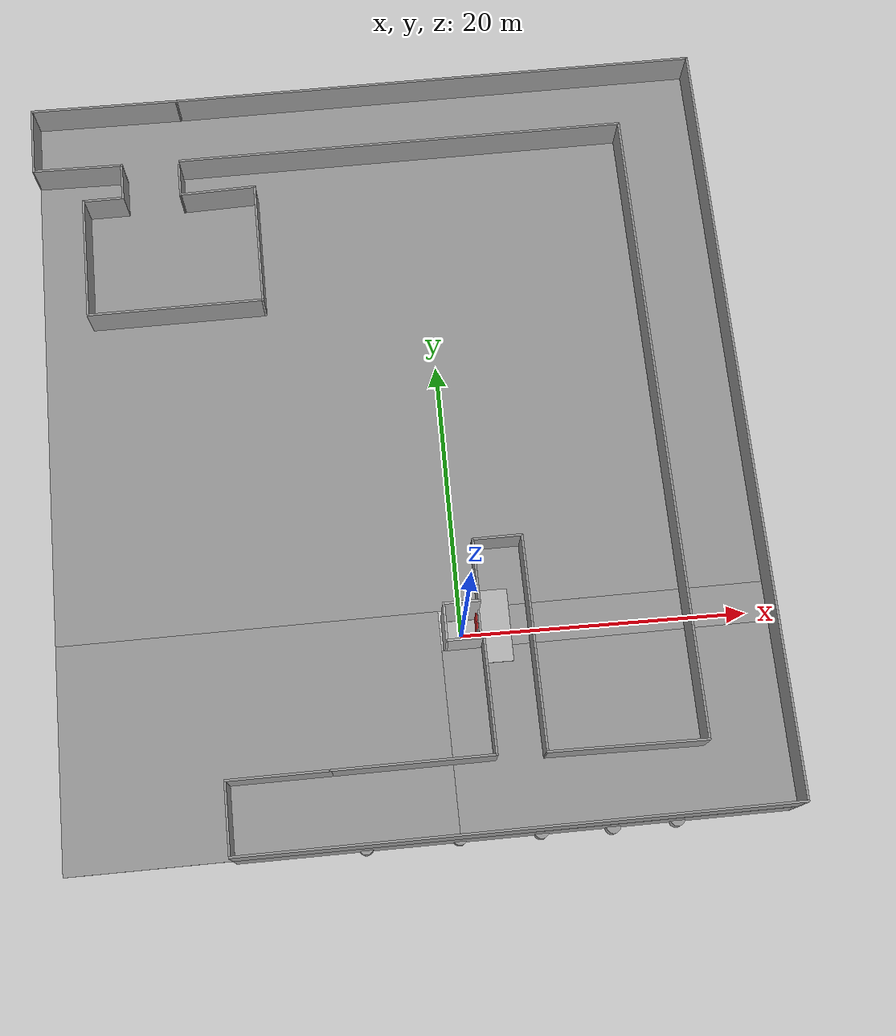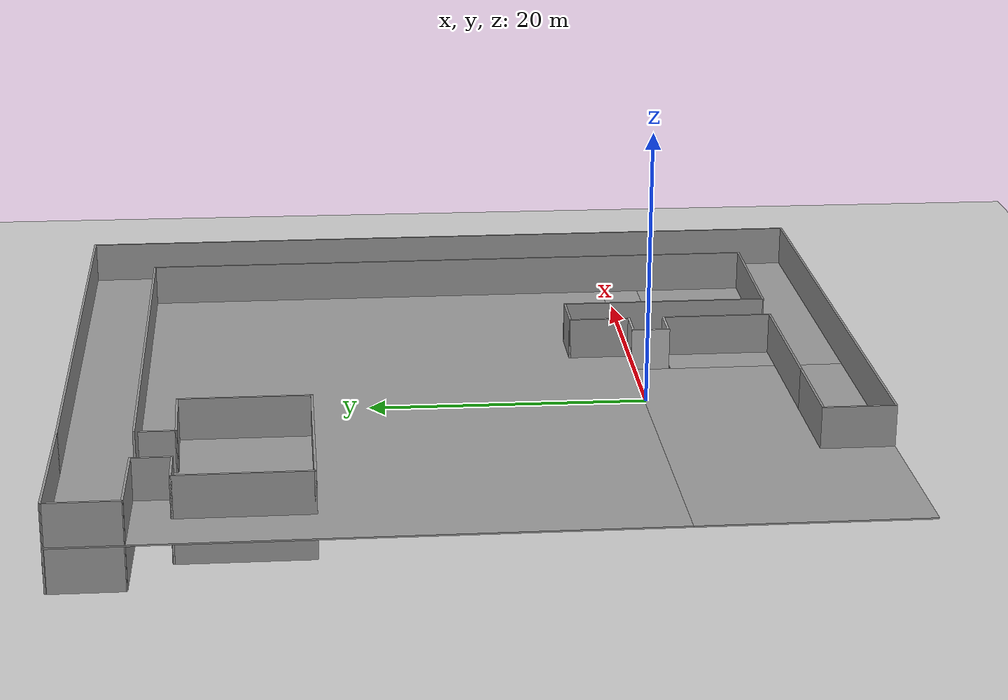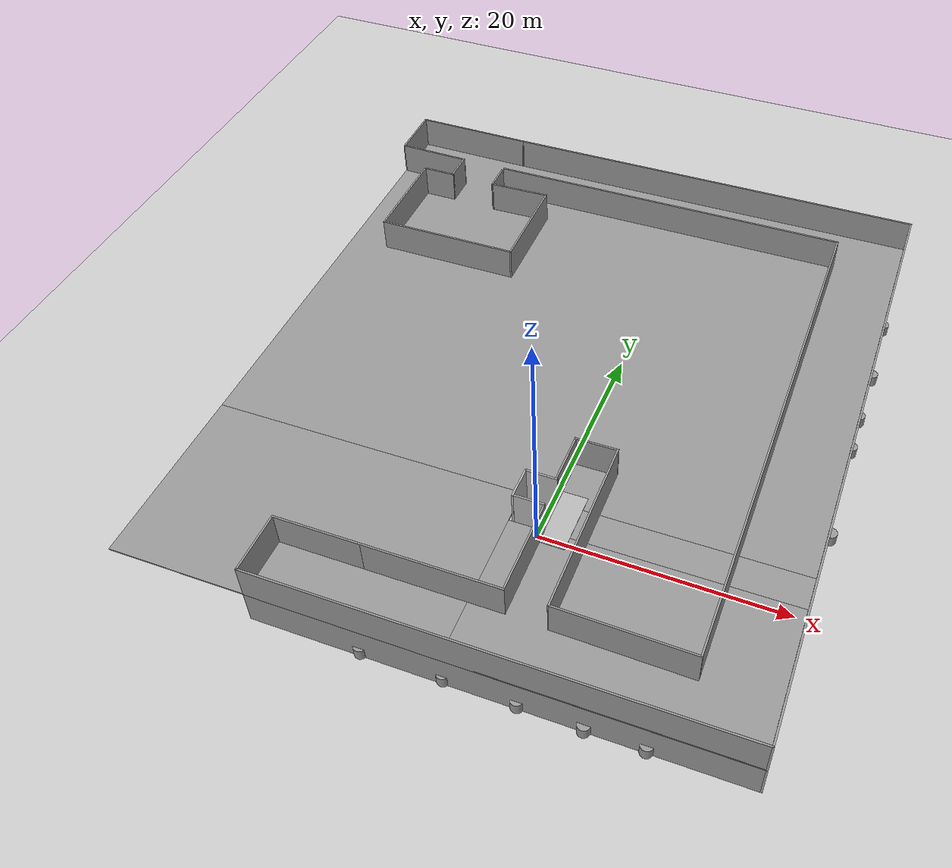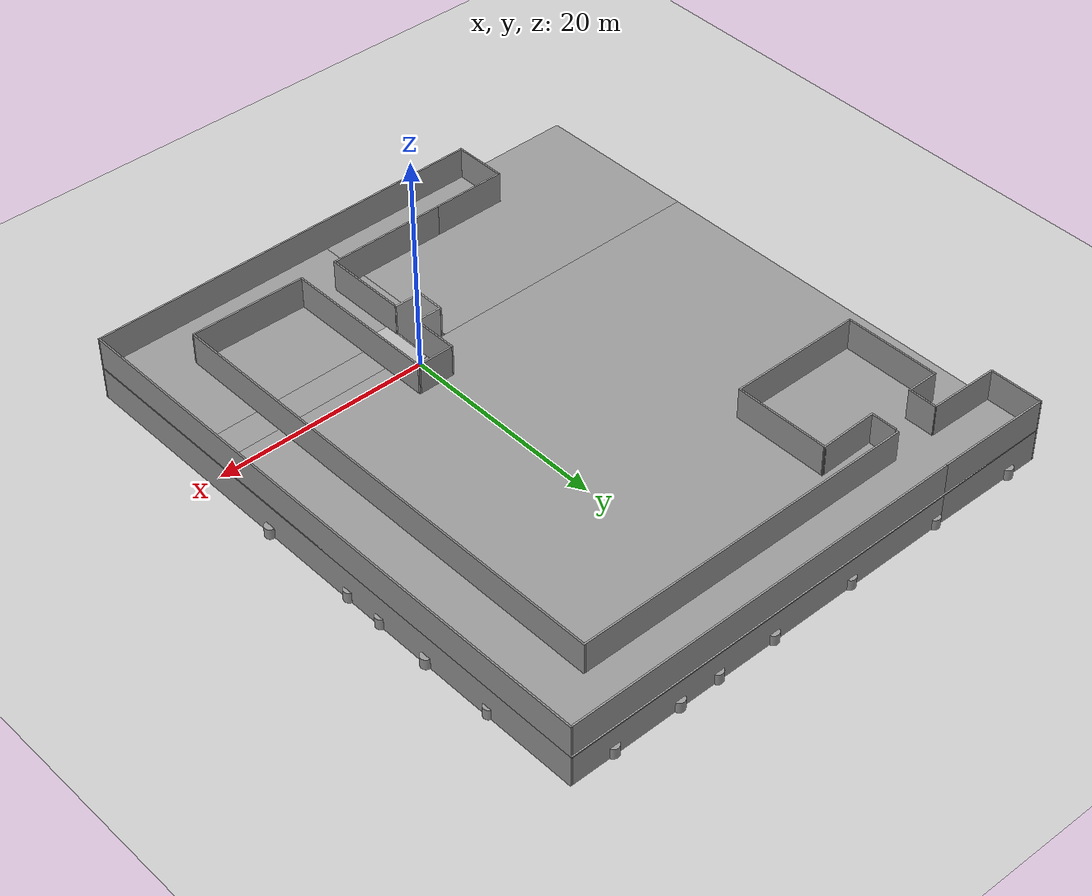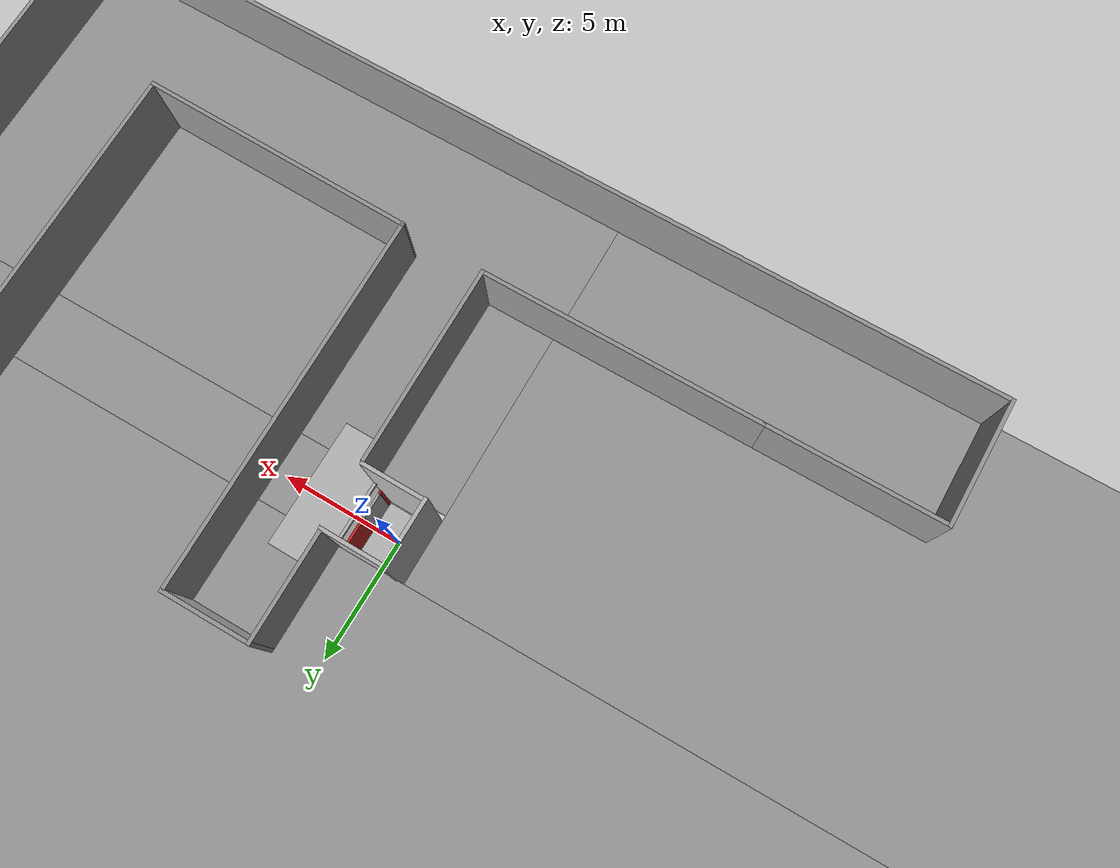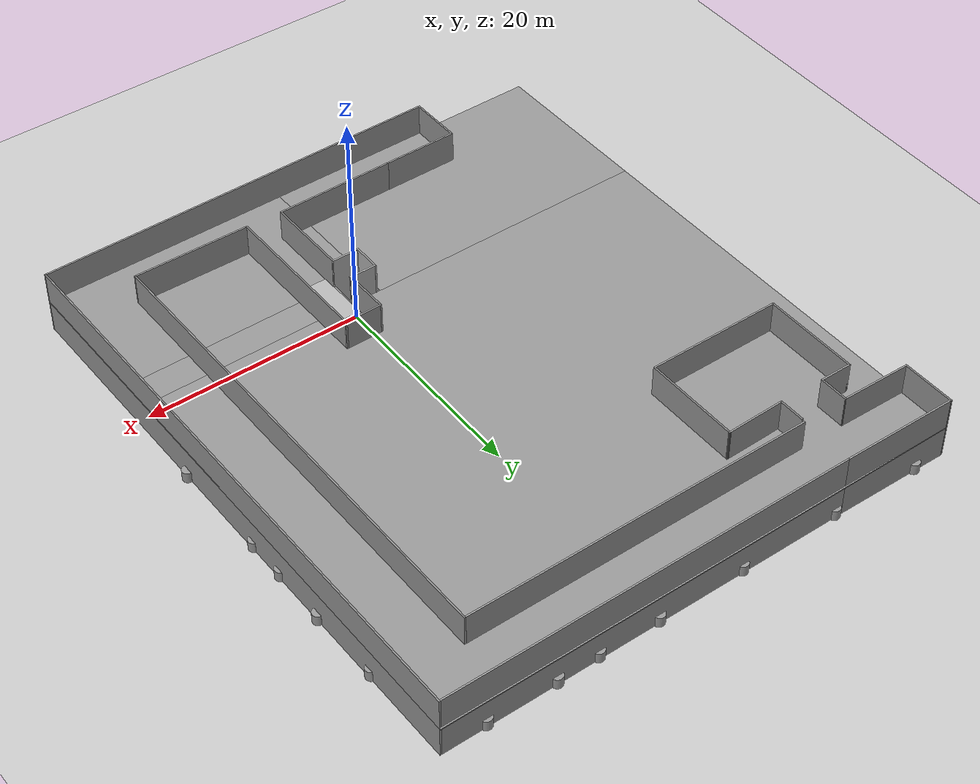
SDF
<sdf version="1.7">
 <world name="default">
  <light name="sun" type="directional">
   <pose>0 0 10 0 -0 0</pose>
   <diffuse>0.8 0.8 0.8 1</diffuse>
   <specular>0.2 0.2 0.2 1</specular>
   <attenuation>
    <range>1000</range>
    <constant>0.9</constant>
    <linear>0.01</linear>
    <quadratic>0.001</quadratic>
   </attenuation>
   <direction>-0.5 0.1 -0.9</direction>
   <spot><inner_angle>0</inner_angle><outer_angle>0</outer_angle><falloff>0</falloff></spot>
  </light>
  <model name="ground_plane">
   <static>1</static>
   <link name="link">
    <collision name="collision">
     <geometry><plane><normal>0 0 1</normal><size>100 100</size></plane></geometry>
     <surface><friction><ode><mu>100</mu><mu2>50</mu2></ode></friction></surface>
    </collision>
    <visual name="visual">
     <cast_shadows>0</cast_shadows>
     <geometry><plane><normal>0 0 1</normal><size>100 100</size></plane></geometry>
     <material>
      <script><uri>file://media/materials/scripts/gazebo.material</uri><name>Gazebo/Grey</name></script>
     </material>
    </visual>
   </link>
  </model>
  <plugin name="elevator_event_plugin" filename="libSimEventsPlugin.so">
   <region><name>region1</name><volume><min>1.5 -1 0</min><max>2.5 1 1</max></volume></region>
   <region><name>region2</name><volume><min>1.5 -1 3</min><max>2.5 1 4</max></volume></region>
   <event>
    <name>region1_event</name>
    <type>occupied</type>
    <region>region1</region>
    <topic>~/elevator</topic>
    <msg_data>0</msg_data>
   </event>
   <event>
    <name>region2_event</name>
    <type>occupied</type>
    <region>region2</region>
    <topic>~/elevator</topic>
    <msg_data>1</msg_data>
   </event>
  </plugin>
  <model name="elevator">
   <pose>-0 -0 0.075 -0 -0 -2e-06</pose>
   <link name="link">
    <inertial>
     <mass>800</mass>
     <inertia><ixx>1</ixx><ixy>0</ixy><ixz>0</ixz><iyy>1</iyy><iyz>0</iyz><izz>1</izz></inertia>
    </inertial>
    <collision name="floor_collision"><geometry><box><size>2.25 2.25 0.15</size></box></geometry></collision>
    <visual name="floor_visual"><geometry><box><size>2.25 2.25 0.15</size></box></geometry></visual>
    <collision name="wall1_collision">
     <pose>1.0745 0.5725 1.125 0 -0 0</pose>
     <geometry><box><size>0.1 1.15 2.25</size></box></geometry>
    </collision>
    <visual name="wall1_visual">
     <pose>1.0745 0.5725 1.125 0 -0 0</pose>
     <geometry><box><size>0.1 1.15 2.25</size></box></geometry>
     <material><script><name>Gazebo/Red</name><uri>__default__</uri></script></material>
    </visual>
    <collision name="wall2_collision">
     <pose>1.0745 -1.0625 1.125 0 -0 0</pose>
     <geometry><box><size>0.1 0.125 2.25</size></box></geometry>
    </collision>
    <visual name="wall2_visual">
     <pose>1.0745 -1.0625 1.125 0 -0 0</pose>
     <geometry><box><size>0.1 0.125 2.25</size></box></geometry>
     <material><script><name>Gazebo/Red</name><uri>__default__</uri></script></material>
    </visual>
   </link>
   <link name="door">
    <pose>1.0745 -0.5 1.125 0 -0 0</pose>
    <collision name="collision"><geometry><box><size>0.08 1 2.25</size></box></geometry></collision>
    <visual name="visual"><geometry><box><size>0.08 1 2.25</size></box></geometry></visual>
    <inertial>
     <inertia><ixx>1</ixx><ixy>0</ixy><ixz>0</ixz><iyy>1</iyy><iyz>0</iyz><izz>1</izz></inertia>
     <mass>1</mass>
    </inertial>
   </link>
   <joint name="door" type="prismatic">
    <parent>link</parent>
    <child>door</child>
    <axis>
     <xyz>0 1 0</xyz>
     <limit><lower>0</lower><upper>1</upper><effort>10</effort></limit>
     <dynamics>
      <damping>2</damping>
      <spring_reference>0</spring_reference>
      <spring_stiffness>0</spring_stiffness>
     </dynamics>
    </axis>
   </joint>
   <joint name="lift" type="prismatic">
    <parent>world</parent>
    <child>link</child>
    <axis>
     <xyz>0 0 1</xyz>
     <limit><lower>0</lower><upper>10</upper><effort>100000</effort></limit>
     <dynamics>
      <damping>50</damping>
      <spring_reference>0</spring_reference>
      <spring_stiffness>0</spring_stiffness>
     </dynamics>
    </axis>
    <physics>
     <ode><implicit_spring_damper>1</implicit_spring_damper><limit><cfm>0</cfm><erp>0.2</erp></limit></ode>
    </physics>
   </joint>
   <plugin name="elevator_plugin" filename="libElevatorPlugin.so">
    <lift_joint>elevator::lift</lift_joint>
    <door_joint>elevator::door</door_joint>
    <floor_height>3.075</floor_height>
    <door_wait_time>10</door_wait_time>
    <topic>~/elevator</topic>
   </plugin>
  </model>
  <model name="elevator_shaft">
   <static>1</static>
   <link name="link">
    <collision name="shaft_wall1_collision">
     <pose>0 1.25 3 0 -0 0</pose>
     <geometry><box><size>2.5 0.15 6</size></box></geometry>
    </collision>
    <visual name="shaft_wall1_visual">
     <pose>0 1.25 3 0 -0 0</pose>
     <geometry><box><size>2.5 0.15 6</size></box></geometry>
    </visual>
    <collision name="shaft_wall2_collision">
     <pose>0 -1.25 3 0 -0 0</pose>
     <geometry><box><size>2.5 0.15 6</size></box></geometry>
    </collision>
    <visual name="shaft_wall2_visual">
     <pose>0 -1.25 3 0 -0 0</pose>
     <geometry><box><size>2.5 0.15 6</size></box></geometry>
    </visual>
    <collision name="shaft_wall3_collision">
     <pose>-1.25 0 3 0 -0 0</pose>
     <geometry><box><size>0.15 2.7 6</size></box></geometry>
    </collision>
    <visual name="shaft_wall3_visual">
     <pose>-1.25 0 3 0 -0 0</pose>
     <geometry><box><size>0.15 2.7 6</size></box></geometry>
    </visual>
    <collision name="floor0_collision">
     <pose>1.19 0 0.075 0 -0 0</pose>
     <geometry><box><size>0.12 2.5 0.15</size></box></geometry>
    </collision>
    <visual name="floor0_visual">
     <pose>1.19 0 0.075 0 -0 0</pose>
     <geometry><box><size>0.12 2.5 0.15</size></box></geometry>
    </visual>
    <collision name="floor1_collision">
     <pose>1.19 0 3.075 0 -0 0</pose>
     <geometry><box><size>0.12 2.5 0.15</size></box></geometry>
    </collision>
    <visual name="floor1_visual">
     <pose>1.19 0 3.075 0 -0 0</pose>
     <geometry><box><size>0.12 2.5 0.15</size></box></geometry>
    </visual>
   </link>
  </model>
  <model name="floor1">
   <pose>2.25 0 3.075 0 -0 0</pose>
   <static>1</static>
   <link name="link">
    <collision name="floor_collision"><geometry><box><size>2 5 0.15</size></box></geometry></collision>
    <visual name="floor_visual"><geometry><box><size>2 5 0.15</size></box></geometry></visual>
   </link>
  </model>
  <gravity>0 0 -9.8</gravity>
  <magnetic_field>6e-06 2.3e-05 -4.2e-05</magnetic_field>
  <atmosphere type="adiabatic"/>
  <physics name="default_physics" default="0" type="ode">
   <max_step_size>0.001</max_step_size>
   <real_time_factor>1</real_time_factor>
   <real_time_update_rate>1000</real_time_update_rate>
  </physics>
  <scene><ambient>0.4 0.4 0.4 1</ambient><background>0.7 0.7 0.7 1</background><shadows>1</shadows></scene>
  <audio><device>default</device></audio>
  <spherical_coordinates>
   <surface_model>EARTH_WGS84</surface_model>
   <latitude_deg>0</latitude_deg>
   <longitude_deg>0</longitude_deg>
   <elevation>0</elevation>
   <heading_deg>0</heading_deg>
  </spherical_coordinates>
  <model name="hakjunv1">
   <pose>-3.51672 13.3502 0 0 0 -1.56017</pose>
   <link name="Floor_0">
    <pose>0 1e-06 3 0 -0 0</pose>
    <visual name="Floor_0_Visual_0">
     <pose>-7.63092 0 0.05 0 -0 0</pose>
     <geometry><box><size>39.363 48.6014 0.1</size></box></geometry>
     <material>
      <script><uri>file://media/materials/scripts/gazebo.material</uri><name>Gazebo/Grey</name></script>
      <ambient>1 1 1 1</ambient>
     </material>
     <meta><layer>1</layer></meta>
    </visual>
    <collision name="Floor_0_Collision_0">
     <geometry><box><size>39.363 48.6014 0.1</size></box></geometry>
     <pose>-7.63092 0 0.05 0 -0 0</pose>
    </collision>
    <visual name="Floor_0_Visual_1">
     <pose>19.6815 -11.2522 0.05 0 -0 0</pose>
     <geometry><box><size>15.2618 26.097 0.1</size></box></geometry>
     <material>
      <script><uri>file://media/materials/scripts/gazebo.material</uri><name>Gazebo/Grey</name></script>
      <ambient>1 1 1 1</ambient>
     </material>
     <meta><layer>1</layer></meta>
    </visual>
    <collision name="Floor_0_Collision_1">
     <geometry><box><size>15.2618 26.097 0.1</size></box></geometry>
     <pose>19.6815 -11.2522 0.05 0 -0 0</pose>
    </collision>
    <visual name="Floor_0_Visual_2">
     <pose>21.0615 13.0485 0.05 0 -0 0</pose>
     <geometry><box><size>12.5018 22.5044 0.1</size></box></geometry>
     <material>
      <script><uri>file://media/materials/scripts/gazebo.material</uri><name>Gazebo/Grey</name></script>
      <ambient>1 1 1 1</ambient>
     </material>
     <meta><layer>1</layer></meta>
    </visual>
    <collision name="Floor_0_Collision_2">
     <geometry><box><size>12.5018 22.5044 0.1</size></box></geometry>
     <pose>21.0615 13.0485 0.05 0 -0 0</pose>
    </collision>
    <visual name="Floor_0_Visual_3">
     <pose>13.4306 14.4285 0.05 0 -0 0</pose>
     <geometry><box><size>2.76 19.7444 0.1</size></box></geometry>
     <material>
      <script><uri>file://media/materials/scripts/gazebo.material</uri><name>Gazebo/Grey</name></script>
      <ambient>1 1 1 1</ambient>
     </material>
     <meta><layer>1</layer></meta>
    </visual>
    <collision name="Floor_0_Collision_3">
     <geometry><box><size>2.76 19.7444 0.1</size></box></geometry>
     <pose>13.4306 14.4285 0.05 0 -0 0</pose>
    </collision>
   </link>
   <link name="Wall_0">
    <collision name="Wall_0_Collision">
     <geometry><box><size>4.25 0.15 3</size></box></geometry>
     <pose>0 0 1.5 0 -0 0</pose>
    </collision>
    <visual name="Wall_0_Visual">
     <pose>0 0 1.5 0 -0 0</pose>
     <geometry><box><size>4.25 0.15 3</size></box></geometry>
     <material>
      <script><uri>file://media/materials/scripts/gazebo.material</uri><name>Gazebo/Grey</name></script>
      <ambient>1 1 1 1</ambient>
     </material>
     <meta><layer>0</layer></meta>
    </visual>
    <pose>9.97344 4.53073 0 0 -0 3.14159</pose>
   </link>
   <link name="Wall_1">
    <collision name="Wall_1_Collision">
     <geometry><box><size>3.5 0.15 3</size></box></geometry>
     <pose>0 0 1.5 0 -0 0</pose>
    </collision>
    <visual name="Wall_1_Visual">
     <pose>0 0 1.5 0 -0 0</pose>
     <geometry><box><size>3.5 0.15 3</size></box></geometry>
     <material>
      <script><uri>file://media/materials/scripts/gazebo.material</uri><name>Gazebo/Grey</name></script>
      <ambient>1 1 1 1</ambient>
     </material>
     <meta><layer>0</layer></meta>
    </visual>
    <pose>7.92344 6.20573 0 0 -0 1.5708</pose>
   </link>
   <link name="Wall_10">
    <collision name="Wall_10_Collision">
     <geometry><box><size>5 0.15 3</size></box></geometry>
     <pose>0 0 1.5 0 -0 0</pose>
    </collision>
    <visual name="Wall_10_Visual">
     <pose>0 0 1.5 0 -0 0</pose>
     <geometry><box><size>5 0.15 3</size></box></geometry>
     <material>
      <script><uri>file://media/materials/scripts/gazebo.material</uri><name>Gazebo/Grey</name></script>
      <ambient>1 1 1 1</ambient>
     </material>
     <meta><layer>0</layer></meta>
    </visual>
    <pose>24.8124 -13.1243 0 0 -0 0</pose>
   </link>
   <link name="Wall_11">
    <collision name="Wall_11_Collision">
     <geometry><box><size>37.5 0.15 3</size></box></geometry>
     <pose>0 0 1.5 0 -0 0</pose>
    </collision>
    <visual name="Wall_11_Visual">
     <pose>0 0 1.5 0 -0 0</pose>
     <geometry><box><size>37.5 0.15 3</size></box></geometry>
     <material>
      <script><uri>file://media/materials/scripts/gazebo.material</uri><name>Gazebo/Grey</name></script>
      <ambient>1 1 1 1</ambient>
     </material>
     <meta><layer>0</layer></meta>
    </visual>
    <pose>27.2374 5.55072 0 0 -0 1.5708</pose>
   </link>
   <link name="Wall_13">
    <collision name="Wall_13_Collision">
     <geometry><box><size>10.7517 0.15 3</size></box></geometry>
     <pose>0 0 1.5 0 -0 0</pose>
    </collision>
    <visual name="Wall_13_Visual">
     <pose>0 0 1.5 0 -0 0</pose>
     <geometry><box><size>10.7517 0.15 3</size></box></geometry>
     <material>
      <script><uri>file://media/materials/scripts/gazebo.material</uri><name>Gazebo/Grey</name></script>
      <ambient>1 1 1 1</ambient>
     </material>
     <meta><layer>0</layer></meta>
    </visual>
    <pose>22.617 13.1807 0 0 -0 1.55314</pose>
   </link>
   <link name="Wall_15">
    <collision name="Wall_15_Collision">
     <geometry><box><size>45 0.15 3</size></box></geometry>
     <pose>0 0 1.5 0 -0 0</pose>
    </collision>
    <visual name="Wall_15_Visual">
     <pose>0 0 1.5 0 -0 0</pose>
     <geometry><box><size>45 0.15 3</size></box></geometry>
     <material>
      <script><uri>file://media/materials/scripts/gazebo.material</uri><name>Gazebo/Grey</name></script>
      <ambient>1 1 1 1</ambient>
     </material>
     <meta><layer>0</layer></meta>
    </visual>
    <pose>0.192225 18.4807 0 0 -0 3.14159</pose>
   </link>
   <link name="Wall_17">
    <collision name="Wall_17_Collision">
     <geometry><box><size>54.5 0.15 3</size></box></geometry>
     <pose>0 0 1.5 0 -0 0</pose>
    </collision>
    <visual name="Wall_17_Visual">
     <pose>0 0 1.5 0 -0 0</pose>
     <geometry><box><size>54.5 0.15 3</size></box></geometry>
     <material>
      <script><uri>file://media/materials/scripts/gazebo.material</uri><name>Gazebo/Grey</name></script>
      <ambient>1 1 1 1</ambient>
     </material>
     <meta><layer>0</layer></meta>
    </visual>
    <pose>0.062436 24.2257 0 0 -0 3.14159</pose>
   </link>
   <link name="Wall_19">
    <collision name="Wall_19_Collision">
     <geometry><box><size>32.25 0.15 3</size></box></geometry>
     <pose>0 0 1.5 0 -0 0</pose>
    </collision>
    <visual name="Wall_19_Visual">
     <pose>0 0 1.5 0 -0 0</pose>
     <geometry><box><size>32.25 0.15 3</size></box></geometry>
     <material>
      <script><uri>file://media/materials/scripts/gazebo.material</uri><name>Gazebo/Grey</name></script>
      <ambient>1 1 1 1</ambient>
     </material>
     <meta><layer>0</layer></meta>
    </visual>
    <pose>-22.2326 2.43073 0 0 -0 -1.5708</pose>
   </link>
   <link name="Wall_2">
    <collision name="Wall_2_Collision">
     <geometry><box><size>14.75 0.15 3</size></box></geometry>
     <pose>0 0 1.5 0 -0 0</pose>
    </collision>
    <visual name="Wall_2_Visual">
     <pose>0 0 1.5 0 -0 0</pose>
     <geometry><box><size>14.75 0.15 3</size></box></geometry>
     <material>
      <script><uri>file://media/materials/scripts/gazebo.material</uri><name>Gazebo/Grey</name></script>
      <ambient>1 1 1 1</ambient>
     </material>
     <meta><layer>0</layer></meta>
    </visual>
    <pose>15.2234 7.88072 0 0 -0 0</pose>
   </link>
   <link name="Wall_22">
    <collision name="Wall_22_Collision">
     <geometry><box><size>38 0.15 3</size></box></geometry>
     <pose>0 0 1.5 0 -0 0</pose>
    </collision>
    <visual name="Wall_22_Visual">
     <pose>0 0 1.5 0 -0 0</pose>
     <geometry><box><size>38 0.15 3</size></box></geometry>
     <material>
      <script><uri>file://media/materials/scripts/gazebo.material</uri><name>Gazebo/Grey</name></script>
      <ambient>1 1 1 1</ambient>
     </material>
     <meta><layer>0</layer></meta>
    </visual>
    <pose>-27.1126 5.30072 0 0 -0 -1.5708</pose>
   </link>
   <link name="Wall_24">
    <collision name="Wall_24_Collision">
     <geometry><box><size>10.75 0.15 3</size></box></geometry>
     <pose>0 0 1.5 0 -0 0</pose>
    </collision>
    <visual name="Wall_24_Visual">
     <pose>0 0 1.5 0 -0 0</pose>
     <geometry><box><size>10.75 0.15 3</size></box></geometry>
     <material>
      <script><uri>file://media/materials/scripts/gazebo.material</uri><name>Gazebo/Grey</name></script>
      <ambient>1 1 1 1</ambient>
     </material>
     <meta><layer>0</layer></meta>
    </visual>
    <pose>-27.1746 -18.9243 0 0 -0 -1.58249</pose>
   </link>
   <link name="Wall_25">
    <collision name="Wall_25_Collision">
     <geometry><box><size>5 0.15 3</size></box></geometry>
     <pose>0 0 1.5 0 -0 0</pose>
    </collision>
    <visual name="Wall_25_Visual">
     <pose>0 0 1.5 0 -0 0</pose>
     <geometry><box><size>5 0.15 3</size></box></geometry>
     <material>
      <script><uri>file://media/materials/scripts/gazebo.material</uri><name>Gazebo/Grey</name></script>
      <ambient>1 1 1 1</ambient>
     </material>
     <meta><layer>0</layer></meta>
    </visual>
    <pose>-24.8116 -24.2243 0 0 -0 0</pose>
   </link>
   <link name="Wall_26">
    <collision name="Wall_26_Collision">
     <geometry><box><size>6.50121 0.15 3</size></box></geometry>
     <pose>0 0 1.5 0 -0 0</pose>
    </collision>
    <visual name="Wall_26_Visual">
     <pose>0 0 1.5 0 -0 0</pose>
     <geometry><box><size>6.50121 0.15 3</size></box></geometry>
     <material>
      <script><uri>file://media/materials/scripts/gazebo.material</uri><name>Gazebo/Grey</name></script>
      <ambient>1 1 1 1</ambient>
     </material>
     <meta><layer>0</layer></meta>
    </visual>
    <pose>-22.3246 -21.0493 0 0 -0 1.55127</pose>
   </link>
   <link name="Wall_29">
    <collision name="Wall_29_Collision">
     <geometry><box><size>2.75 0.15 3</size></box></geometry>
     <pose>0 0 1.5 0 -0 0</pose>
    </collision>
    <visual name="Wall_29_Visual">
     <pose>0 0 1.5 0 -0 0</pose>
     <geometry><box><size>2.75 0.15 3</size></box></geometry>
     <material>
      <script><uri>file://media/materials/scripts/gazebo.material</uri><name>Gazebo/Grey</name></script>
      <ambient>1 1 1 1</ambient>
     </material>
     <meta><layer>0</layer></meta>
    </visual>
    <pose>-20.9626 -17.8743 0 0 -0 0</pose>
   </link>
   <link name="Wall_30">
    <collision name="Wall_30_Collision">
     <geometry><box><size>3 0.15 3</size></box></geometry>
     <pose>0 0 1.5 0 -0 0</pose>
    </collision>
    <visual name="Wall_30_Visual">
     <pose>0 0 1.5 0 -0 0</pose>
     <geometry><box><size>3 0.15 3</size></box></geometry>
     <material>
      <script><uri>file://media/materials/scripts/gazebo.material</uri><name>Gazebo/Grey</name></script>
      <ambient>1 1 1 1</ambient>
     </material>
     <meta><layer>0</layer></meta>
    </visual>
    <pose>-19.6626 -19.2993 0 0 -0 -1.5708</pose>
   </link>
   <link name="Wall_31">
    <collision name="Wall_31_Collision">
     <geometry><box><size>9 0.15 3</size></box></geometry>
     <pose>0 0 1.5 0 -0 0</pose>
    </collision>
    <visual name="Wall_31_Visual">
     <pose>0 0 1.5 0 -0 0</pose>
     <geometry><box><size>9 0.15 3</size></box></geometry>
     <material>
      <script><uri>file://media/materials/scripts/gazebo.material</uri><name>Gazebo/Grey</name></script>
      <ambient>1 1 1 1</ambient>
     </material>
     <meta><layer>0</layer></meta>
    </visual>
    <pose>-15.2376 -20.7243 0 0 -0 0</pose>
   </link>
   <link name="Wall_32">
    <collision name="Wall_32_Collision">
     <geometry><box><size>12.5 0.15 3</size></box></geometry>
     <pose>0 0 1.5 0 -0 0</pose>
    </collision>
    <visual name="Wall_32_Visual">
     <pose>0 0 1.5 0 -0 0</pose>
     <geometry><box><size>12.5 0.15 3</size></box></geometry>
     <material>
      <script><uri>file://media/materials/scripts/gazebo.material</uri><name>Gazebo/Grey</name></script>
      <ambient>1 1 1 1</ambient>
     </material>
     <meta><layer>0</layer></meta>
    </visual>
    <pose>-10.8126 -14.5493 0 0 -0 1.5708</pose>
   </link>
   <link name="Wall_33">
    <collision name="Wall_33_Collision">
     <geometry><box><size>9 0.15 3</size></box></geometry>
     <pose>0 0 1.5 0 -0 0</pose>
    </collision>
    <visual name="Wall_33_Visual">
     <pose>0 0 1.5 0 -0 0</pose>
     <geometry><box><size>9 0.15 3</size></box></geometry>
     <material>
      <script><uri>file://media/materials/scripts/gazebo.material</uri><name>Gazebo/Grey</name></script>
      <ambient>1 1 1 1</ambient>
     </material>
     <meta><layer>0</layer></meta>
    </visual>
    <pose>-15.2376 -8.37427 0 0 -0 3.14159</pose>
   </link>
   <link name="Wall_34">
    <collision name="Wall_34_Collision">
     <geometry><box><size>5.50144 0.15 3</size></box></geometry>
     <pose>0 0 1.5 0 -0 0</pose>
    </collision>
    <visual name="Wall_34_Visual">
     <pose>0 0 1.5 0 -0 0</pose>
     <geometry><box><size>5.50144 0.15 3</size></box></geometry>
     <material>
      <script><uri>file://media/materials/scripts/gazebo.material</uri><name>Gazebo/Grey</name></script>
      <ambient>1 1 1 1</ambient>
     </material>
     <meta><layer>0</layer></meta>
    </visual>
    <pose>-19.6006 -11.0493 0 0 -0 -1.54762</pose>
   </link>
   <link name="Wall_35">
    <collision name="Wall_35_Collision">
     <geometry><box><size>2.5 0.15 3</size></box></geometry>
     <pose>0 0 1.5 0 -0 0</pose>
    </collision>
    <visual name="Wall_35_Visual">
     <pose>0 0 1.5 0 -0 0</pose>
     <geometry><box><size>2.5 0.15 3</size></box></geometry>
     <material>
      <script><uri>file://media/materials/scripts/gazebo.material</uri><name>Gazebo/Grey</name></script>
      <ambient>1 1 1 1</ambient>
     </material>
     <meta><layer>0</layer></meta>
    </visual>
    <pose>-20.7136 -13.7243 0 0 -0 3.14159</pose>
   </link>
   <link name="Wall_37">
    <collision name="Wall_37_Collision">
     <geometry><box><size>4.25 0.15 3</size></box></geometry>
     <pose>0 0 1.5 0 -0 0</pose>
    </collision>
    <visual name="Wall_37_Visual">
     <pose>0 0 1.5 0 -0 0</pose>
     <geometry><box><size>4.25 0.15 3</size></box></geometry>
     <material>
      <script><uri>file://media/materials/scripts/gazebo.material</uri><name>Gazebo/Grey</name></script>
      <ambient>1 1 1 1</ambient>
     </material>
     <meta><layer>1</layer></meta>
    </visual>
    <pose>9.97344 4.53073 3 0 -0 3.14159</pose>
   </link>
   <link name="Wall_38">
    <collision name="Wall_38_Collision">
     <geometry><box><size>3.5 0.15 3</size></box></geometry>
     <pose>0 0 1.5 0 -0 0</pose>
    </collision>
    <visual name="Wall_38_Visual">
     <pose>0 0 1.5 0 -0 0</pose>
     <geometry><box><size>3.5 0.15 3</size></box></geometry>
     <material>
      <script><uri>file://media/materials/scripts/gazebo.material</uri><name>Gazebo/Grey</name></script>
      <ambient>1 1 1 1</ambient>
     </material>
     <meta><layer>1</layer></meta>
    </visual>
    <pose>7.92344 6.20573 3 0 -0 1.5708</pose>
   </link>
   <link name="Wall_39">
    <collision name="Wall_39_Collision">
     <geometry><box><size>14.75 0.15 3</size></box></geometry>
     <pose>0 0 1.5 0 -0 0</pose>
    </collision>
    <visual name="Wall_39_Visual">
     <pose>0 0 1.5 0 -0 0</pose>
     <geometry><box><size>14.75 0.15 3</size></box></geometry>
     <material>
      <script><uri>file://media/materials/scripts/gazebo.material</uri><name>Gazebo/Grey</name></script>
      <ambient>1 1 1 1</ambient>
     </material>
     <meta><layer>1</layer></meta>
    </visual>
    <pose>15.2234 7.88072 3 0 -0 0</pose>
   </link>
   <link name="Wall_4">
    <collision name="Wall_4_Collision">
     <geometry><box><size>7.75 0.15 3</size></box></geometry>
     <pose>0 0 1.5 0 -0 0</pose>
    </collision>
    <visual name="Wall_4_Visual">
     <pose>0 0 1.5 0 -0 0</pose>
     <geometry><box><size>7.75 0.15 3</size></box></geometry>
     <material>
      <script><uri>file://media/materials/scripts/gazebo.material</uri><name>Gazebo/Grey</name></script>
      <ambient>1 1 1 1</ambient>
     </material>
     <meta><layer>0</layer></meta>
    </visual>
    <pose>18.5874 4.57573 0 0 -0 0</pose>
   </link>
   <link name="Wall_40">
    <collision name="Wall_40_Collision">
     <geometry><box><size>7.75 0.15 3</size></box></geometry>
     <pose>0 0 1.5 0 -0 0</pose>
    </collision>
    <visual name="Wall_40_Visual">
     <pose>0 0 1.5 0 -0 0</pose>
     <geometry><box><size>7.75 0.15 3</size></box></geometry>
     <material>
      <script><uri>file://media/materials/scripts/gazebo.material</uri><name>Gazebo/Grey</name></script>
      <ambient>1 1 1 1</ambient>
     </material>
     <meta><layer>1</layer></meta>
    </visual>
    <pose>18.5874 4.57573 3 0 -0 0</pose>
   </link>
   <link name="Wall_41">
    <collision name="Wall_41_Collision">
     <geometry><box><size>11 0.15 3</size></box></geometry>
     <pose>0 0 1.5 0 -0 0</pose>
    </collision>
    <visual name="Wall_41_Visual">
     <pose>0 0 1.5 0 -0 0</pose>
     <geometry><box><size>11 0.15 3</size></box></geometry>
     <material>
      <script><uri>file://media/materials/scripts/gazebo.material</uri><name>Gazebo/Grey</name></script>
      <ambient>1 1 1 1</ambient>
     </material>
     <meta><layer>1</layer></meta>
    </visual>
    <pose>22.3874 -0.849275 3 0 -0 -1.5708</pose>
   </link>
   <link name="Wall_42">
    <collision name="Wall_42_Collision">
     <geometry><box><size>7 0.15 3</size></box></geometry>
     <pose>0 0 1.5 0 -0 0</pose>
    </collision>
    <visual name="Wall_42_Visual">
     <pose>0 0 1.5 0 -0 0</pose>
     <geometry><box><size>7 0.15 3</size></box></geometry>
     <material>
      <script><uri>file://media/materials/scripts/gazebo.material</uri><name>Gazebo/Grey</name></script>
      <ambient>1 1 1 1</ambient>
     </material>
     <meta><layer>1</layer></meta>
    </visual>
    <pose>22.3874 -9.69928 3 0 -0 -1.5708</pose>
   </link>
   <link name="Wall_43">
    <collision name="Wall_43_Collision">
     <geometry><box><size>5 0.15 3</size></box></geometry>
     <pose>0 0 1.5 0 -0 0</pose>
    </collision>
    <visual name="Wall_43_Visual">
     <pose>0 0 1.5 0 -0 0</pose>
     <geometry><box><size>5 0.15 3</size></box></geometry>
     <material>
      <script><uri>file://media/materials/scripts/gazebo.material</uri><name>Gazebo/Grey</name></script>
      <ambient>1 1 1 1</ambient>
     </material>
     <meta><layer>1</layer></meta>
    </visual>
    <pose>24.8124 -13.1243 3 0 -0 0</pose>
   </link>
   <link name="Wall_44">
    <collision name="Wall_44_Collision">
     <geometry><box><size>37.5 0.15 3</size></box></geometry>
     <pose>0 0 1.5 0 -0 0</pose>
    </collision>
    <visual name="Wall_44_Visual">
     <pose>0 0 1.5 0 -0 0</pose>
     <geometry><box><size>37.5 0.15 3</size></box></geometry>
     <material>
      <script><uri>file://media/materials/scripts/gazebo.material</uri><name>Gazebo/Grey</name></script>
      <ambient>1 1 1 1</ambient>
     </material>
     <meta><layer>1</layer></meta>
    </visual>
    <pose>27.2374 5.55072 3 0 -0 1.5708</pose>
   </link>
   <link name="Wall_45">
    <collision name="Wall_45_Collision">
     <geometry><box><size>10.7517 0.15 3</size></box></geometry>
     <pose>0 0 1.5 0 -0 0</pose>
    </collision>
    <visual name="Wall_45_Visual">
     <pose>0 0 1.5 0 -0 0</pose>
     <geometry><box><size>10.7517 0.15 3</size></box></geometry>
     <material>
      <script><uri>file://media/materials/scripts/gazebo.material</uri><name>Gazebo/Grey</name></script>
      <ambient>1 1 1 1</ambient>
     </material>
     <meta><layer>1</layer></meta>
    </visual>
    <pose>22.617 13.1807 3 0 -0 1.55314</pose>
   </link>
   <link name="Wall_46">
    <collision name="Wall_46_Collision">
     <geometry><box><size>44.9996 0.15 3</size></box></geometry>
     <pose>0 0 1.5 0 -0 0</pose>
    </collision>
    <visual name="Wall_46_Visual">
     <pose>0 0 1.5 0 -0 0</pose>
     <geometry><box><size>44.9996 0.15 3</size></box></geometry>
     <material>
      <script><uri>file://media/materials/scripts/gazebo.material</uri><name>Gazebo/Grey</name></script>
      <ambient>1 1 1 1</ambient>
     </material>
     <meta><layer>1</layer></meta>
    </visual>
    <pose>0.192224 18.4807 3 0 -0 3.14159</pose>
   </link>
   <link name="Wall_47">
    <collision name="Wall_47_Collision">
     <geometry><box><size>54.5 0.15 3</size></box></geometry>
     <pose>0 0 1.5 0 -0 0</pose>
    </collision>
    <visual name="Wall_47_Visual">
     <pose>0 0 1.5 0 -0 0</pose>
     <geometry><box><size>54.5 0.15 3</size></box></geometry>
     <material>
      <script><uri>file://media/materials/scripts/gazebo.material</uri><name>Gazebo/Grey</name></script>
      <ambient>1 1 1 1</ambient>
     </material>
     <meta><layer>1</layer></meta>
    </visual>
    <pose>0.062436 24.2257 3 0 -0 3.14159</pose>
   </link>
   <link name="Wall_48">
    <collision name="Wall_48_Collision">
     <geometry><box><size>32.25 0.15 3</size></box></geometry>
     <pose>0 0 1.5 0 -0 0</pose>
    </collision>
    <visual name="Wall_48_Visual">
     <pose>0 0 1.5 0 -0 0</pose>
     <geometry><box><size>32.25 0.15 3</size></box></geometry>
     <material>
      <script><uri>file://media/materials/scripts/gazebo.material</uri><name>Gazebo/Grey</name></script>
      <ambient>1 1 1 1</ambient>
     </material>
     <meta><layer>1</layer></meta>
    </visual>
    <pose>-22.2326 2.43072 3 0 -0 -1.5708</pose>
   </link>
   <link name="Wall_49">
    <collision name="Wall_49_Collision">
     <geometry><box><size>38 0.15 3</size></box></geometry>
     <pose>0 0 1.5 0 -0 0</pose>
    </collision>
    <visual name="Wall_49_Visual">
     <pose>0 0 1.5 0 -0 0</pose>
     <geometry><box><size>38 0.15 3</size></box></geometry>
     <material>
      <script><uri>file://media/materials/scripts/gazebo.material</uri><name>Gazebo/Grey</name></script>
      <ambient>1 1 1 1</ambient>
     </material>
     <meta><layer>1</layer></meta>
    </visual>
    <pose>-27.1126 5.30072 3 0 -0 -1.5708</pose>
   </link>
   <link name="Wall_50">
    <collision name="Wall_50_Collision">
     <geometry><box><size>10.7507 0.15 3</size></box></geometry>
     <pose>0 0 1.5 0 -0 0</pose>
    </collision>
    <visual name="Wall_50_Visual">
     <pose>0 0 1.5 0 -0 0</pose>
     <geometry><box><size>10.7507 0.15 3</size></box></geometry>
     <material>
      <script><uri>file://media/materials/scripts/gazebo.material</uri><name>Gazebo/Grey</name></script>
      <ambient>1 1 1 1</ambient>
     </material>
     <meta><layer>1</layer></meta>
    </visual>
    <pose>-27.1746 -18.9243 3 0 -0 -1.58249</pose>
   </link>
   <link name="Wall_51">
    <collision name="Wall_51_Collision">
     <geometry><box><size>5 0.15 3</size></box></geometry>
     <pose>0 0 1.5 0 -0 0</pose>
    </collision>
    <visual name="Wall_51_Visual">
     <pose>0 0 1.5 0 -0 0</pose>
     <geometry><box><size>5 0.15 3</size></box></geometry>
     <material>
      <script><uri>file://media/materials/scripts/gazebo.material</uri><name>Gazebo/Grey</name></script>
      <ambient>1 1 1 1</ambient>
     </material>
     <meta><layer>1</layer></meta>
    </visual>
    <pose>-24.8116 -24.2243 3 0 -0 0</pose>
   </link>
   <link name="Wall_52">
    <collision name="Wall_52_Collision">
     <geometry><box><size>6.50121 0.15 3</size></box></geometry>
     <pose>0 0 1.5 0 -0 0</pose>
    </collision>
    <visual name="Wall_52_Visual">
     <pose>0 0 1.5 0 -0 0</pose>
     <geometry><box><size>6.50121 0.15 3</size></box></geometry>
     <material>
      <script><uri>file://media/materials/scripts/gazebo.material</uri><name>Gazebo/Grey</name></script>
      <ambient>1 1 1 1</ambient>
     </material>
     <meta><layer>1</layer></meta>
    </visual>
    <pose>-22.3246 -21.0493 3 0 -0 1.55127</pose>
   </link>
   <link name="Wall_53">
    <collision name="Wall_53_Collision">
     <geometry><box><size>2.75 0.15 3</size></box></geometry>
     <pose>0 0 1.5 0 -0 0</pose>
    </collision>
    <visual name="Wall_53_Visual">
     <pose>0 0 1.5 0 -0 0</pose>
     <geometry><box><size>2.75 0.15 3</size></box></geometry>
     <material>
      <script><uri>file://media/materials/scripts/gazebo.material</uri><name>Gazebo/Grey</name></script>
      <ambient>1 1 1 1</ambient>
     </material>
     <meta><layer>1</layer></meta>
    </visual>
    <pose>-20.9626 -17.8743 3 0 -0 0</pose>
   </link>
   <link name="Wall_54">
    <collision name="Wall_54_Collision">
     <geometry><box><size>3 0.15 3</size></box></geometry>
     <pose>0 0 1.5 0 -0 0</pose>
    </collision>
    <visual name="Wall_54_Visual">
     <pose>0 0 1.5 0 -0 0</pose>
     <geometry><box><size>3 0.15 3</size></box></geometry>
     <material>
      <script><uri>file://media/materials/scripts/gazebo.material</uri><name>Gazebo/Grey</name></script>
      <ambient>1 1 1 1</ambient>
     </material>
     <meta><layer>1</layer></meta>
    </visual>
    <pose>-19.6626 -19.2993 3 0 -0 -1.5708</pose>
   </link>
   <link name="Wall_55">
    <collision name="Wall_55_Collision">
     <geometry><box><size>9 0.15 3</size></box></geometry>
     <pose>0 0 1.5 0 -0 0</pose>
    </collision>
    <visual name="Wall_55_Visual">
     <pose>0 0 1.5 0 -0 0</pose>
     <geometry><box><size>9 0.15 3</size></box></geometry>
     <material>
      <script><uri>file://media/materials/scripts/gazebo.material</uri><name>Gazebo/Grey</name></script>
      <ambient>1 1 1 1</ambient>
     </material>
     <meta><layer>1</layer></meta>
    </visual>
    <pose>-15.2376 -20.7243 3 0 -0 0</pose>
   </link>
   <link name="Wall_56">
    <collision name="Wall_56_Collision">
     <geometry><box><size>12.5 0.15 3</size></box></geometry>
     <pose>0 0 1.5 0 -0 0</pose>
    </collision>
    <visual name="Wall_56_Visual">
     <pose>0 0 1.5 0 -0 0</pose>
     <geometry><box><size>12.5 0.15 3</size></box></geometry>
     <material>
      <script><uri>file://media/materials/scripts/gazebo.material</uri><name>Gazebo/Grey</name></script>
      <ambient>1 1 1 1</ambient>
     </material>
     <meta><layer>1</layer></meta>
    </visual>
    <pose>-10.8126 -14.5493 3 0 -0 1.5708</pose>
   </link>
   <link name="Wall_57">
    <collision name="Wall_57_Collision">
     <geometry><box><size>9 0.15 3</size></box></geometry>
     <pose>0 0 1.5 0 -0 0</pose>
    </collision>
    <visual name="Wall_57_Visual">
     <pose>0 0 1.5 0 -0 0</pose>
     <geometry><box><size>9 0.15 3</size></box></geometry>
     <material>
      <script><uri>file://media/materials/scripts/gazebo.material</uri><name>Gazebo/Grey</name></script>
      <ambient>1 1 1 1</ambient>
     </material>
     <meta><layer>1</layer></meta>
    </visual>
    <pose>-15.2376 -8.37427 3 0 -0 3.14159</pose>
   </link>
   <link name="Wall_58">
    <collision name="Wall_58_Collision">
     <geometry><box><size>5.50144 0.15 3</size></box></geometry>
     <pose>0 0 1.5 0 -0 0</pose>
    </collision>
    <visual name="Wall_58_Visual">
     <pose>0 0 1.5 0 -0 0</pose>
     <geometry><box><size>5.50144 0.15 3</size></box></geometry>
     <material>
      <script><uri>file://media/materials/scripts/gazebo.material</uri><name>Gazebo/Grey</name></script>
      <ambient>1 1 1 1</ambient>
     </material>
     <meta><layer>1</layer></meta>
    </visual>
    <pose>-19.6006 -11.0493 3 0 -0 -1.54762</pose>
   </link>
   <link name="Wall_59">
    <collision name="Wall_59_Collision">
     <geometry><box><size>2.5 0.15 3</size></box></geometry>
     <pose>0 0 1.5 0 -0 0</pose>
    </collision>
    <visual name="Wall_59_Visual">
     <pose>0 0 1.5 0 -0 0</pose>
     <geometry><box><size>2.5 0.15 3</size></box></geometry>
     <material>
      <script><uri>file://media/materials/scripts/gazebo.material</uri><name>Gazebo/Grey</name></script>
      <ambient>1 1 1 1</ambient>
     </material>
     <meta><layer>1</layer></meta>
    </visual>
    <pose>-20.7136 -13.7243 3 0 -0 3.14159</pose>
   </link>
   <link name="Wall_6">
    <collision name="Wall_6_Collision">
     <geometry><box><size>11 0.15 3</size></box></geometry>
     <pose>0 0 1.5 0 -0 0</pose>
    </collision>
    <visual name="Wall_6_Visual">
     <pose>0 0 1.5 0 -0 0</pose>
     <geometry><box><size>11 0.15 3</size></box></geometry>
     <material>
      <script><uri>file://media/materials/scripts/gazebo.material</uri><name>Gazebo/Grey</name></script>
      <ambient>1 1 1 1</ambient>
     </material>
     <meta><layer>0</layer></meta>
    </visual>
    <pose>22.3874 -0.849275 0 0 -0 -1.5708</pose>
   </link>
   <link name="Wall_9">
    <collision name="Wall_9_Collision">
     <geometry><box><size>7 0.15 3</size></box></geometry>
     <pose>0 0 1.5 0 -0 0</pose>
    </collision>
    <visual name="Wall_9_Visual">
     <pose>0 0 1.5 0 -0 0</pose>
     <geometry><box><size>7 0.15 3</size></box></geometry>
     <material>
      <script><uri>file://media/materials/scripts/gazebo.material</uri><name>Gazebo/Grey</name></script>
      <ambient>1 1 1 1</ambient>
     </material>
     <meta><layer>0</layer></meta>
    </visual>
    <pose>22.3874 -9.69928 0 0 -0 -1.5708</pose>
   </link>
   <static>1</static>
  </model>
  <model name="unit_cylinder">
   <pose>-9.38863 35.494 0.499994 -1e-06 -0 -0</pose>
   <link name="link">
    <inertial>
     <mass>1</mass>
     <inertia><ixx>0.145833</ixx><ixy>0</ixy><ixz>0</ixz><iyy>0.145833</iyy><iyz>0</iyz><izz>0.125</izz></inertia>
    </inertial>
    <collision name="collision">
     <geometry><cylinder><radius>0.5</radius><length>1</length></cylinder></geometry>
    </collision>
    <visual name="visual">
     <geometry><cylinder><radius>0.5</radius><length>1</length></cylinder></geometry>
     <material>
      <script><name>Gazebo/Grey</name><uri>file://media/materials/scripts/gazebo.material</uri></script>
     </material>
    </visual>
   </link>
  </model>
  <model name="unit_cylinder_0">
   <pose>-7.52435 40.3235 0.499996 0 -0 0</pose>
   <link name="link">
    <inertial>
     <mass>1</mass>
     <inertia><ixx>0.145833</ixx><ixy>0</ixy><ixz>0</ixz><iyy>0.145833</iyy><iyz>0</iyz><izz>0.125</izz></inertia>
    </inertial>
    <collision name="collision">
     <geometry><cylinder><radius>0.5</radius><length>1</length></cylinder></geometry>
    </collision>
    <visual name="visual">
     <geometry><cylinder><radius>0.5</radius><length>1</length></cylinder></geometry>
     <material>
      <script><name>Gazebo/Grey</name><uri>file://media/materials/scripts/gazebo.material</uri></script>
     </material>
    </visual>
   </link>
  </model>
  <model name="unit_cylinder_1">
   <pose>0.617778 40.4666 0.499996 0 -0 0</pose>
   <link name="link">
    <inertial>
     <mass>1</mass>
     <inertia><ixx>0.145833</ixx><ixy>0</ixy><ixz>0</ixz><iyy>0.145833</iyy><iyz>0</iyz><izz>0.125</izz></inertia>
    </inertial>
    <collision name="collision">
     <geometry><cylinder><radius>0.5</radius><length>1</length></cylinder></geometry>
    </collision>
    <visual name="visual">
     <geometry><cylinder><radius>0.5</radius><length>1</length></cylinder></geometry>
     <material>
      <script><name>Gazebo/Grey</name><uri>file://media/materials/scripts/gazebo.material</uri></script>
     </material>
    </visual>
   </link>
  </model>
  <model name="unit_cylinder_2">
   <pose>6.24023 40.4826 0.499996 0 -0 0</pose>
   <link name="link">
    <inertial>
     <mass>1</mass>
     <inertia><ixx>0.145833</ixx><ixy>0</ixy><ixz>0</ixz><iyy>0.145833</iyy><iyz>0</iyz><izz>0.125</izz></inertia>
    </inertial>
    <collision name="collision">
     <geometry><cylinder><radius>0.5</radius><length>1</length></cylinder></geometry>
    </collision>
    <visual name="visual">
     <geometry><cylinder><radius>0.5</radius><length>1</length></cylinder></geometry>
     <material>
      <script><name>Gazebo/Grey</name><uri>file://media/materials/scripts/gazebo.material</uri></script>
     </material>
    </visual>
   </link>
  </model>
  <model name="unit_cylinder_3">
   <pose>10.0843 40.5766 0.499994 -1e-06 -0 -0</pose>
   <link name="link">
    <inertial>
     <mass>1</mass>
     <inertia><ixx>0.145833</ixx><ixy>0</ixy><ixz>0</ixz><iyy>0.145833</iyy><iyz>0</iyz><izz>0.125</izz></inertia>
    </inertial>
    <collision name="collision">
     <geometry><cylinder><radius>0.5</radius><length>1</length></cylinder></geometry>
    </collision>
    <visual name="visual">
     <geometry><cylinder><radius>0.5</radius><length>1</length></cylinder></geometry>
     <material>
      <script><name>Gazebo/Grey</name><uri>file://media/materials/scripts/gazebo.material</uri></script>
     </material>
    </visual>
   </link>
  </model>
  <model name="unit_cylinder_4">
   <pose>16.3555 40.5832 0.499996 0 -0 0</pose>
   <link name="link">
    <inertial>
     <mass>1</mass>
     <inertia><ixx>0.145833</ixx><ixy>0</ixy><ixz>0</ixz><iyy>0.145833</iyy><iyz>0</iyz><izz>0.125</izz></inertia>
    </inertial>
    <collision name="collision">
     <geometry><cylinder><radius>0.5</radius><length>1</length></cylinder></geometry>
    </collision>
    <visual name="visual">
     <geometry><cylinder><radius>0.5</radius><length>1</length></cylinder></geometry>
     <material>
      <script><name>Gazebo/Grey</name><uri>file://media/materials/scripts/gazebo.material</uri></script>
     </material>
    </visual>
   </link>
  </model>
  <model name="unit_cylinder_5">
   <pose>-16.8539 40.2258 0.499994 -3e-06 -1e-06 -0</pose>
   <link name="link">
    <inertial>
     <mass>1</mass>
     <inertia><ixx>0.145833</ixx><ixy>0</ixy><ixz>0</ixz><iyy>0.145833</iyy><iyz>0</iyz><izz>0.125</izz></inertia>
    </inertial>
    <collision name="collision">
     <geometry><cylinder><radius>0.5</radius><length>1</length></cylinder></geometry>
    </collision>
    <visual name="visual">
     <geometry><cylinder><radius>0.5</radius><length>1</length></cylinder></geometry>
     <material>
      <script><name>Gazebo/Grey</name><uri>file://media/materials/scripts/gazebo.material</uri></script>
     </material>
    </visual>
   </link>
  </model>
  <model name="unit_cylinder_6">
   <pose>-25.1098 40.2944 0.499996 0 -0 0</pose>
   <link name="link">
    <inertial>
     <mass>1</mass>
     <inertia><ixx>0.145833</ixx><ixy>0</ixy><ixz>0</ixz><iyy>0.145833</iyy><iyz>0</iyz><izz>0.125</izz></inertia>
    </inertial>
    <collision name="collision">
     <geometry><cylinder><radius>0.5</radius><length>1</length></cylinder></geometry>
    </collision>
    <visual name="visual">
     <geometry><cylinder><radius>0.5</radius><length>1</length></cylinder></geometry>
     <material>
      <script><name>Gazebo/Grey</name><uri>file://media/materials/scripts/gazebo.material</uri></script>
     </material>
    </visual>
   </link>
  </model>
  <model name="unit_box">
   <pose>4.7013 35.0962 0.499995 -0 -1e-05 0.010622</pose>
   <link name="link">
    <inertial>
     <mass>1</mass>
     <inertia>
      <ixx>0.166667</ixx>
      <ixy>0</ixy>
      <ixz>0</ixz>
      <iyy>0.166667</iyy>
      <iyz>0</iyz>
      <izz>0.166667</izz>
     </inertia>
    </inertial>
    <collision name="collision"><geometry><box><size>1 1 1</size></box></geometry></collision>
    <visual name="visual">
     <geometry><box><size>1 1 1</size></box></geometry>
     <material>
      <script><name>Gazebo/Grey</name><uri>file://media/materials/scripts/gazebo.material</uri></script>
     </material>
    </visual>
   </link>
  </model>
  <model name="unit_cylinder_7">
   <pose>2.53194 35.6517 0.499996 0 -0 0</pose>
   <link name="link">
    <inertial>
     <mass>1</mass>
     <inertia><ixx>0.145833</ixx><ixy>0</ixy><ixz>0</ixz><iyy>0.145833</iyy><iyz>0</iyz><izz>0.125</izz></inertia>
    </inertial>
    <collision name="collision">
     <geometry><cylinder><radius>0.5</radius><length>1</length></cylinder></geometry>
    </collision>
    <visual name="visual">
     <geometry><cylinder><radius>0.5</radius><length>1</length></cylinder></geometry>
     <material>
      <script><name>Gazebo/Grey</name><uri>file://media/materials/scripts/gazebo.material</uri></script>
     </material>
    </visual>
   </link>
  </model>
  <model name="unit_box_0">
   <pose>6.46002 35.1149 0.499995 1e-05 0 0.01062</pose>
   <link name="link">
    <inertial>
     <mass>1</mass>
     <inertia>
      <ixx>0.166667</ixx>
      <ixy>0</ixy>
      <ixz>0</ixz>
      <iyy>0.166667</iyy>
      <iyz>0</iyz>
      <izz>0.166667</izz>
     </inertia>
    </inertial>
    <collision name="collision"><geometry><box><size>1 1 1</size></box></geometry></collision>
    <visual name="visual">
     <geometry><box><size>1 1 1</size></box></geometry>
     <material>
      <script><name>Gazebo/Grey</name><uri>file://media/materials/scripts/gazebo.material</uri></script>
     </material>
    </visual>
   </link>
  </model>
  <model name="unit_cylinder_8">
   <pose>11.955 35.666 0.499996 0 -0 0</pose>
   <link name="link">
    <inertial>
     <mass>1</mass>
     <inertia><ixx>0.145833</ixx><ixy>0</ixy><ixz>0</ixz><iyy>0.145833</iyy><iyz>0</iyz><izz>0.125</izz></inertia>
    </inertial>
    <collision name="collision">
     <geometry><cylinder><radius>0.5</radius><length>1</length></cylinder></geometry>
    </collision>
    <visual name="visual">
     <geometry><cylinder><radius>0.5</radius><length>1</length></cylinder></geometry>
     <material>
      <script><name>Gazebo/Grey</name><uri>file://media/materials/scripts/gazebo.material</uri></script>
     </material>
    </visual>
   </link>
  </model>
  <model name="unit_cylinder_9">
   <pose>20.3909 32.183 0.499993 -1e-06 -0 0</pose>
   <link name="link">
    <inertial>
     <mass>1</mass>
     <inertia><ixx>0.145833</ixx><ixy>0</ixy><ixz>0</ixz><iyy>0.145833</iyy><iyz>0</iyz><izz>0.125</izz></inertia>
    </inertial>
    <collision name="collision">
     <geometry><cylinder><radius>0.5</radius><length>1</length></cylinder></geometry>
    </collision>
    <visual name="visual">
     <geometry><cylinder><radius>0.5</radius><length>1</length></cylinder></geometry>
     <material>
      <script><name>Gazebo/Grey</name><uri>file://media/materials/scripts/gazebo.material</uri></script>
     </material>
    </visual>
   </link>
  </model>
  <model name="unit_cylinder_10">
   <pose>20.6191 25.6191 0.499996 0 -0 0</pose>
   <link name="link">
    <inertial>
     <mass>1</mass>
     <inertia><ixx>0.145833</ixx><ixy>0</ixy><ixz>0</ixz><iyy>0.145833</iyy><iyz>0</iyz><izz>0.125</izz></inertia>
    </inertial>
    <collision name="collision">
     <geometry><cylinder><radius>0.5</radius><length>1</length></cylinder></geometry>
    </collision>
    <visual name="visual">
     <geometry><cylinder><radius>0.5</radius><length>1</length></cylinder></geometry>
     <material>
      <script><name>Gazebo/Grey</name><uri>file://media/materials/scripts/gazebo.material</uri></script>
     </material>
    </visual>
   </link>
  </model>
  <model name="unit_cylinder_11">
   <pose>20.5462 20.4255 0.499993 -1e-06 -0 0</pose>
   <link name="link">
    <inertial>
     <mass>1</mass>
     <inertia><ixx>0.145833</ixx><ixy>0</ixy><ixz>0</ixz><iyy>0.145833</iyy><iyz>0</iyz><izz>0.125</izz></inertia>
    </inertial>
    <collision name="collision">
     <geometry><cylinder><radius>0.5</radius><length>1</length></cylinder></geometry>
    </collision>
    <visual name="visual">
     <geometry><cylinder><radius>0.5</radius><length>1</length></cylinder></geometry>
     <material>
      <script><name>Gazebo/Grey</name><uri>file://media/materials/scripts/gazebo.material</uri></script>
     </material>
    </visual>
   </link>
  </model>
  <model name="unit_cylinder_12">
   <pose>20.5958 16.8 0.499996 0 -0 0</pose>
   <link name="link">
    <inertial>
     <mass>1</mass>
     <inertia><ixx>0.145833</ixx><ixy>0</ixy><ixz>0</ixz><iyy>0.145833</iyy><iyz>0</iyz><izz>0.125</izz></inertia>
    </inertial>
    <collision name="collision">
     <geometry><cylinder><radius>0.5</radius><length>1</length></cylinder></geometry>
    </collision>
    <visual name="visual">
     <geometry><cylinder><radius>0.5</radius><length>1</length></cylinder></geometry>
     <material>
      <script><name>Gazebo/Grey</name><uri>file://media/materials/scripts/gazebo.material</uri></script>
     </material>
    </visual>
   </link>
  </model>
  <model name="unit_cylinder_13">
   <pose>20.8798 7.6408 0.499993 -1e-06 -0 0</pose>
   <link name="link">
    <inertial>
     <mass>1</mass>
     <inertia><ixx>0.145833</ixx><ixy>0</ixy><ixz>0</ixz><iyy>0.145833</iyy><iyz>0</iyz><izz>0.125</izz></inertia>
    </inertial>
    <collision name="collision">
     <geometry><cylinder><radius>0.5</radius><length>1</length></cylinder></geometry>
    </collision>
    <visual name="visual">
     <geometry><cylinder><radius>0.5</radius><length>1</length></cylinder></geometry>
     <material>
      <script><name>Gazebo/Grey</name><uri>file://media/materials/scripts/gazebo.material</uri></script>
     </material>
    </visual>
   </link>
  </model>
  <model name="unit_cylinder_14">
   <pose>14.8081 30.7206 0.499996 0 -0 0</pose>
   <link name="link">
    <inertial>
     <mass>1</mass>
     <inertia><ixx>0.145833</ixx><ixy>0</ixy><ixz>0</ixz><iyy>0.145833</iyy><iyz>0</iyz><izz>0.125</izz></inertia>
    </inertial>
    <collision name="collision">
     <geometry><cylinder><radius>0.5</radius><length>1</length></cylinder></geometry>
    </collision>
    <visual name="visual">
     <geometry><cylinder><radius>0.5</radius><length>1</length></cylinder></geometry>
     <material>
      <script><name>Gazebo/Grey</name><uri>file://media/materials/scripts/gazebo.material</uri></script>
     </material>
    </visual>
   </link>
  </model>
  <model name="unit_cylinder_15">
   <pose>14.9752 12.7015 0.499993 -1e-06 -0 0</pose>
   <link name="link">
    <inertial>
     <mass>1</mass>
     <inertia><ixx>0.145833</ixx><ixy>0</ixy><ixz>0</ixz><iyy>0.145833</iyy><iyz>0</iyz><izz>0.125</izz></inertia>
    </inertial>
    <collision name="collision">
     <geometry><cylinder><radius>0.5</radius><length>1</length></cylinder></geometry>
    </collision>
    <visual name="visual">
     <geometry><cylinder><radius>0.5</radius><length>1</length></cylinder></geometry>
     <material>
      <script><name>Gazebo/Grey</name><uri>file://media/materials/scripts/gazebo.material</uri></script>
     </material>
    </visual>
   </link>
  </model>
  <model name="unit_cylinder_16">
   <pose>14.9174 20.3156 0.499996 0 -0 0</pose>
   <link name="link">
    <inertial>
     <mass>1</mass>
     <inertia><ixx>0.145833</ixx><ixy>0</ixy><ixz>0</ixz><iyy>0.145833</iyy><iyz>0</iyz><izz>0.125</izz></inertia>
    </inertial>
    <collision name="collision">
     <geometry><cylinder><radius>0.5</radius><length>1</length></cylinder></geometry>
    </collision>
    <visual name="visual">
     <geometry><cylinder><radius>0.5</radius><length>1</length></cylinder></geometry>
     <material>
      <script><name>Gazebo/Grey</name><uri>file://media/materials/scripts/gazebo.material</uri></script>
     </material>
    </visual>
   </link>
  </model>
  <model name="unit_cylinder_17">
   <pose>15.0925 -8.06606 0.499993 -1e-06 -0 0</pose>
   <link name="link">
    <inertial>
     <mass>1</mass>
     <inertia><ixx>0.145833</ixx><ixy>0</ixy><ixz>0</ixz><iyy>0.145833</iyy><iyz>0</iyz><izz>0.125</izz></inertia>
    </inertial>
    <collision name="collision">
     <geometry><cylinder><radius>0.5</radius><length>1</length></cylinder></geometry>
    </collision>
    <visual name="visual">
     <geometry><cylinder><radius>0.5</radius><length>1</length></cylinder></geometry>
     <material>
      <script><name>Gazebo/Grey</name><uri>file://media/materials/scripts/gazebo.material</uri></script>
     </material>
    </visual>
   </link>
  </model>
  <model name="unit_cylinder_18">
   <pose>13.2609 -13.6825 0.499996 0 -0 0</pose>
   <link name="link">
    <inertial>
     <mass>1</mass>
     <inertia><ixx>0.145833</ixx><ixy>0</ixy><ixz>0</ixz><iyy>0.145833</iyy><iyz>0</iyz><izz>0.125</izz></inertia>
    </inertial>
    <collision name="collision">
     <geometry><cylinder><radius>0.5</radius><length>1</length></cylinder></geometry>
    </collision>
    <visual name="visual">
     <geometry><cylinder><radius>0.5</radius><length>1</length></cylinder></geometry>
     <material>
      <script><name>Gazebo/Grey</name><uri>file://media/materials/scripts/gazebo.material</uri></script>
     </material>
    </visual>
   </link>
  </model>
  <model name="unit_cylinder_19">
   <pose>8.91655 -13.7956 0.499993 -1e-06 -0 0</pose>
   <link name="link">
    <inertial>
     <mass>1</mass>
     <inertia><ixx>0.145833</ixx><ixy>0</ixy><ixz>0</ixz><iyy>0.145833</iyy><iyz>0</iyz><izz>0.125</izz></inertia>
    </inertial>
    <collision name="collision">
     <geometry><cylinder><radius>0.5</radius><length>1</length></cylinder></geometry>
    </collision>
    <visual name="visual">
     <geometry><cylinder><radius>0.5</radius><length>1</length></cylinder></geometry>
     <material>
      <script><name>Gazebo/Grey</name><uri>file://media/materials/scripts/gazebo.material</uri></script>
     </material>
    </visual>
   </link>
  </model>
  <model name="unit_cylinder_20">
   <pose>4.09429 -13.7282 0.499996 0 -0 0</pose>
   <link name="link">
    <inertial>
     <mass>1</mass>
     <inertia><ixx>0.145833</ixx><ixy>0</ixy><ixz>0</ixz><iyy>0.145833</iyy><iyz>0</iyz><izz>0.125</izz></inertia>
    </inertial>
    <collision name="collision">
     <geometry><cylinder><radius>0.5</radius><length>1</length></cylinder></geometry>
    </collision>
    <visual name="visual">
     <geometry><cylinder><radius>0.5</radius><length>1</length></cylinder></geometry>
     <material>
      <script><name>Gazebo/Grey</name><uri>file://media/materials/scripts/gazebo.material</uri></script>
     </material>
    </visual>
   </link>
  </model>
  <model name="unit_cylinder_21">
   <pose>-7.69117 -13.8033 0.499993 -1e-06 -0 0</pose>
   <link name="link">
    <inertial>
     <mass>1</mass>
     <inertia><ixx>0.145833</ixx><ixy>0</ixy><ixz>0</ixz><iyy>0.145833</iyy><iyz>0</iyz><izz>0.125</izz></inertia>
    </inertial>
    <collision name="collision">
     <geometry><cylinder><radius>0.5</radius><length>1</length></cylinder></geometry>
    </collision>
    <visual name="visual">
     <geometry><cylinder><radius>0.5</radius><length>1</length></cylinder></geometry>
     <material>
      <script><name>Gazebo/Grey</name><uri>file://media/materials/scripts/gazebo.material</uri></script>
     </material>
    </visual>
   </link>
  </model>
  <model name="unit_cylinder_22">
   <pose>-6.79754 -9.25639 0.499996 0 -0 0</pose>
   <link name="link">
    <inertial>
     <mass>1</mass>
     <inertia><ixx>0.145833</ixx><ixy>0</ixy><ixz>0</ixz><iyy>0.145833</iyy><iyz>0</iyz><izz>0.125</izz></inertia>
    </inertial>
    <collision name="collision">
     <geometry><cylinder><radius>0.5</radius><length>1</length></cylinder></geometry>
    </collision>
    <visual name="visual">
     <geometry><cylinder><radius>0.5</radius><length>1</length></cylinder></geometry>
     <material>
      <script><name>Gazebo/Grey</name><uri>file://media/materials/scripts/gazebo.material</uri></script>
     </material>
    </visual>
   </link>
  </model>
  <model name="unit_cylinder_23">
   <pose>-13.2069 -9.38891 0.499993 -1e-06 -0 0</pose>
   <link name="link">
    <inertial>
     <mass>1</mass>
     <inertia><ixx>0.145833</ixx><ixy>0</ixy><ixz>0</ixz><iyy>0.145833</iyy><iyz>0</iyz><izz>0.125</izz></inertia>
    </inertial>
    <collision name="collision">
     <geometry><cylinder><radius>0.5</radius><length>1</length></cylinder></geometry>
    </collision>
    <visual name="visual">
     <geometry><cylinder><radius>0.5</radius><length>1</length></cylinder></geometry>
     <material>
      <script><name>Gazebo/Grey</name><uri>file://media/materials/scripts/gazebo.material</uri></script>
     </material>
    </visual>
   </link>
  </model>
  <model name="unit_cylinder_24">
   <pose>-1.39553 -13.6899 0.499993 -1e-06 -0 0</pose>
   <link name="link">
    <inertial>
     <mass>1</mass>
     <inertia><ixx>0.145833</ixx><ixy>0</ixy><ixz>0</ixz><iyy>0.145833</iyy><iyz>0</iyz><izz>0.125</izz></inertia>
    </inertial>
    <collision name="collision">
     <geometry><cylinder><radius>0.5</radius><length>1</length></cylinder></geometry>
    </collision>
    <visual name="visual">
     <geometry><cylinder><radius>0.5</radius><length>1</length></cylinder></geometry>
     <material>
      <script><name>Gazebo/Grey</name><uri>file://media/materials/scripts/gazebo.material</uri></script>
     </material>
    </visual>
   </link>
  </model>
  <model name="unit_box_2_clone">
   <pose>2.87891 -4.08617 0.079638 0 -0.000274 0.005979</pose>
   <link name="link">
    <inertial>
     <mass>1</mass>
     <inertia>
      <ixx>0.166667</ixx>
      <ixy>0</ixy>
      <ixz>0</ixz>
      <iyy>0.166667</iyy>
      <iyz>0</iyz>
      <izz>0.166667</izz>
     </inertia>
    </inertial>
    <collision name="collision"><geometry><box><size>3.07419 0.364988 0.160119</size></box></geometry></collision>
    <visual name="visual">
     <geometry><box><size>3.07419 0.364988 0.160119</size></box></geometry>
     <material>
      <script><name>Gazebo/Grey</name><uri>file://media/materials/scripts/gazebo.material</uri></script>
     </material>
    </visual>
   </link>
  </model>
  <model name="unit_box_2_clone_clone">
   <pose>2.87354 -4.45494 0.074309 -0 -0.000277 0.006428</pose>
   <link name="link">
    <inertial>
     <mass>1</mass>
     <inertia>
      <ixx>0.166667</ixx>
      <ixy>0</ixy>
      <ixz>0</ixz>
      <iyy>0.166667</iyy>
      <iyz>0</iyz>
      <izz>0.166667</izz>
     </inertia>
    </inertial>
    <collision name="collision"><geometry><box><size>3.07419 0.364988 0.149468</size></box></geometry></collision>
    <visual name="visual">
     <geometry><box><size>3.07419 0.364988 0.149468</size></box></geometry>
     <material>
      <script><name>Gazebo/Grey</name><uri>file://media/materials/scripts/gazebo.material</uri></script>
     </material>
    </visual>
   </link>
  </model>
  <model name="unit_box_2_clone_clone_clone">
   <pose>2.88868 -4.83575 0.072865 -0 -3e-06 0.006789</pose>
   <link name="link">
    <inertial>
     <mass>1</mass>
     <inertia>
      <ixx>0.166667</ixx>
      <ixy>0</ixy>
      <ixz>0</ixz>
      <iyy>0.166667</iyy>
      <iyz>0</iyz>
      <izz>0.166667</izz>
     </inertia>
    </inertial>
    <collision name="collision"><geometry><box><size>3.07419 0.364605 0.145741</size></box></geometry></collision>
    <visual name="visual">
     <geometry><box><size>3.07419 0.364605 0.145741</size></box></geometry>
     <material>
      <script><name>Gazebo/Grey</name><uri>file://media/materials/scripts/gazebo.material</uri></script>
     </material>
    </visual>
   </link>
  </model>
  <model name="unit_box_2_clone_clone_clone_clone">
   <pose>2.88835 -5.20255 0.066861 -0 0.00028 0.005877</pose>
   <link name="link">
    <inertial>
     <mass>1</mass>
     <inertia>
      <ixx>0.166667</ixx>
      <ixy>0</ixy>
      <ixz>0</ixz>
      <iyy>0.166667</iyy>
      <iyz>0</iyz>
      <izz>0.166667</izz>
     </inertia>
    </inertial>
    <collision name="collision"><geometry><box><size>3.07419 0.364988 0.134583</size></box></geometry></collision>
    <visual name="visual">
     <geometry><box><size>3.07419 0.364988 0.134583</size></box></geometry>
     <material>
      <script><name>Gazebo/Grey</name><uri>file://media/materials/scripts/gazebo.material</uri></script>
     </material>
    </visual>
   </link>
  </model>
  <model name="unit_box_2_clone_clone_clone_clone_clone">
   <pose>2.88977 -5.56812 0.060117 0 -0.000274 0.005497</pose>
   <link name="link">
    <inertial>
     <mass>1</mass>
     <inertia>
      <ixx>0.166667</ixx>
      <ixy>0</ixy>
      <ixz>0</ixz>
      <iyy>0.166667</iyy>
      <iyz>0</iyz>
      <izz>0.166667</izz>
     </inertia>
    </inertial>
    <collision name="collision"><geometry><box><size>3.07419 0.364988 0.121075</size></box></geometry></collision>
    <visual name="visual">
     <geometry><box><size>3.07419 0.364988 0.121075</size></box></geometry>
     <material>
      <script><name>Gazebo/Grey</name><uri>file://media/materials/scripts/gazebo.material</uri></script>
     </material>
    </visual>
   </link>
  </model>
  <model name="unit_box_2_clone_clone_clone_clone_clone_clone">
   <pose>2.92579 -5.93336 0.056372 0 0.000285 0.005744</pose>
   <link name="link">
    <inertial>
     <mass>1</mass>
     <inertia>
      <ixx>0.166667</ixx>
      <ixy>0</ixy>
      <ixz>0</ixz>
      <iyy>0.166667</iyy>
      <iyz>0</iyz>
      <izz>0.166667</izz>
     </inertia>
    </inertial>
    <collision name="collision"><geometry><box><size>3.07419 0.364988 0.113619</size></box></geometry></collision>
    <visual name="visual">
     <geometry><box><size>3.07419 0.364988 0.113619</size></box></geometry>
     <material>
      <script><name>Gazebo/Grey</name><uri>file://media/materials/scripts/gazebo.material</uri></script>
     </material>
    </visual>
   </link>
  </model>
  <model name="unit_box_2_clone_clone_clone_clone_clone_clone_clone">
   <pose>2.92194 -6.29889 0.050749 0 0.000287 0.005524</pose>
   <link name="link">
    <inertial>
     <mass>1</mass>
     <inertia>
      <ixx>0.166667</ixx>
      <ixy>0</ixy>
      <ixz>0</ixz>
      <iyy>0.166667</iyy>
      <iyz>0</iyz>
      <izz>0.166667</izz>
     </inertia>
    </inertial>
    <collision name="collision"><geometry><box><size>3.07419 0.364988 0.102379</size></box></geometry></collision>
    <visual name="visual">
     <geometry><box><size>3.07419 0.364988 0.102379</size></box></geometry>
     <material>
      <script><name>Gazebo/Grey</name><uri>file://media/materials/scripts/gazebo.material</uri></script>
     </material>
    </visual>
   </link>
  </model>
  <model name="unit_box_2_clone_clone_clone_clone_clone_clone_clone_clone">
   <pose>2.91454 -6.66502 0.044381 0 0.000289 0.005965</pose>
   <link name="link">
    <inertial>
     <mass>1</mass>
     <inertia>
      <ixx>0.166667</ixx>
      <ixy>0</ixy>
      <ixz>0</ixz>
      <iyy>0.166667</iyy>
      <iyz>0</iyz>
      <izz>0.166667</izz>
     </inertia>
    </inertial>
    <collision name="collision">
     <geometry><box><size>3.07419 0.364988 0.0896518</size></box></geometry>
    </collision>
    <visual name="visual">
     <geometry><box><size>3.07419 0.364988 0.0896518</size></box></geometry>
     <material>
      <script><name>Gazebo/Grey</name><uri>file://media/materials/scripts/gazebo.material</uri></script>
     </material>
    </visual>
   </link>
  </model>
  <model name="unit_box_2_clone_clone_clone_clone_clone_clone_clone_clone_clone">
   <pose>2.89727 -7.03731 0.038914 0 -0.000291 0.005951</pose>
   <link name="link">
    <inertial>
     <mass>1</mass>
     <inertia>
      <ixx>0.166667</ixx>
      <ixy>0</ixy>
      <ixz>0</ixz>
      <iyy>0.166667</iyy>
      <iyz>0</iyz>
      <izz>0.166667</izz>
     </inertia>
    </inertial>
    <collision name="collision">
     <geometry><box><size>3.07419 0.375744 0.0787212</size></box></geometry>
    </collision>
    <visual name="visual">
     <geometry><box><size>3.07419 0.375744 0.0787212</size></box></geometry>
     <material>
      <script><name>Gazebo/Grey</name><uri>file://media/materials/scripts/gazebo.material</uri></script>
     </material>
    </visual>
   </link>
  </model>
  <model name="unit_box_2_clone_clone_clone_clone_clone_clone_clone_clone_clone_clone">
   <pose>2.90329 -7.41389 0.033371 -0 -0.000292 0.005292</pose>
   <link name="link">
    <inertial>
     <mass>1</mass>
     <inertia>
      <ixx>0.166667</ixx>
      <ixy>0</ixy>
      <ixz>0</ixz>
      <iyy>0.166667</iyy>
      <iyz>0</iyz>
      <izz>0.166667</izz>
     </inertia>
    </inertial>
    <collision name="collision">
     <geometry><box><size>3.07419 0.374813 0.0676406</size></box></geometry>
    </collision>
    <visual name="visual">
     <geometry><box><size>3.07419 0.374813 0.0676406</size></box></geometry>
     <material>
      <script><name>Gazebo/Grey</name><uri>file://media/materials/scripts/gazebo.material</uri></script>
     </material>
    </visual>
   </link>
  </model>
  <model name="unit_box_2_clone_clone_clone_clone_clone_clone_clone_clone_clone_clone_clone">
   <pose>2.90057 -7.78 0.029277 -1e-06 -0.000293 0.00473</pose>
   <link name="link">
    <inertial>
     <mass>1</mass>
     <inertia>
      <ixx>0.166667</ixx>
      <ixy>0</ixy>
      <ixz>0</ixz>
      <iyy>0.166667</iyy>
      <iyz>0</iyz>
      <izz>0.166667</izz>
     </inertia>
    </inertial>
    <collision name="collision"><geometry><box><size>3.07419 0.35542 0.0594557</size></box></geometry></collision>
    <visual name="visual">
     <geometry><box><size>3.07419 0.35542 0.0594557</size></box></geometry>
     <material>
      <script><name>Gazebo/Grey</name><uri>file://media/materials/scripts/gazebo.material</uri></script>
     </material>
    </visual>
   </link>
  </model>
  <model name="unit_box_2_clone_clone_clone_clone_clone_clone_clone_clone_clone_clone_clone_clone">
   <pose>2.90493 -8.1355 0.024206 -1e-06 0.000293 0.004689</pose>
   <link name="link">
    <inertial>
     <mass>1</mass>
     <inertia>
      <ixx>0.166667</ixx>
      <ixy>0</ixy>
      <ixz>0</ixz>
      <iyy>0.166667</iyy>
      <iyz>0</iyz>
      <izz>0.166667</izz>
     </inertia>
    </inertial>
    <collision name="collision"><geometry><box><size>3.07419 0.35542 0.0493127</size></box></geometry></collision>
    <visual name="visual">
     <geometry><box><size>3.07419 0.35542 0.0493127</size></box></geometry>
     <material>
      <script><name>Gazebo/Grey</name><uri>file://media/materials/scripts/gazebo.material</uri></script>
     </material>
    </visual>
   </link>
  </model>
  <model name="unit_box_2_clone_clone_clone_clone_clone_clone_clone_clone_clone_clone_clone_clone_clone">
   <pose>2.91317 -8.49105 0.020057 -1e-06 -0.000293 0.00458</pose>
   <link name="link">
    <inertial>
     <mass>1</mass>
     <inertia>
      <ixx>0.166667</ixx>
      <ixy>0</ixy>
      <ixz>0</ixz>
      <iyy>0.166667</iyy>
      <iyz>0</iyz>
      <izz>0.166667</izz>
     </inertia>
    </inertial>
    <collision name="collision"><geometry><box><size>3.07419 0.35542 0.0410132</size></box></geometry></collision>
    <visual name="visual">
     <geometry><box><size>3.07419 0.35542 0.0410132</size></box></geometry>
     <material>
      <script><name>Gazebo/Grey</name><uri>file://media/materials/scripts/gazebo.material</uri></script>
     </material>
    </visual>
   </link>
  </model>
  <model name="unit_box_2_clone_clone_0">
   <pose>2.88927 -3.70651 0.08189 1e-06 -0.000273 0.000974</pose>
   <link name="link">
    <inertial>
     <mass>1</mass>
     <inertia>
      <ixx>0.166667</ixx>
      <ixy>0</ixy>
      <ixz>0</ixz>
      <iyy>0.166667</iyy>
      <iyz>0</iyz>
      <izz>0.166667</izz>
     </inertia>
    </inertial>
    <collision name="collision"><geometry><box><size>3.07419 0.364988 0.164618</size></box></geometry></collision>
    <visual name="visual">
     <geometry><box><size>3.07419 0.364988 0.164618</size></box></geometry>
     <material>
      <script><name>Gazebo/Grey</name><uri>file://media/materials/scripts/gazebo.material</uri></script>
     </material>
    </visual>
   </link>
  </model>
  <model name="unit_box_2_clone_clone_0_clone">
   <pose>2.82825 -0.604802 0.080255 0 -3e-06 0.007706</pose>
   <link name="link">
    <inertial>
     <mass>1</mass>
     <inertia>
      <ixx>0.166667</ixx>
      <ixy>0</ixy>
      <ixz>0</ixz>
      <iyy>0.166667</iyy>
      <iyz>0</iyz>
      <izz>0.166667</izz>
     </inertia>
    </inertial>
    <collision name="collision"><geometry><box><size>3.07419 5.7609 0.160519</size></box></geometry></collision>
    <visual name="visual">
     <geometry><box><size>3.07419 5.7609 0.160519</size></box></geometry>
     <material>
      <script><name>Gazebo/Grey</name><uri>file://media/materials/scripts/gazebo.material</uri></script>
     </material>
    </visual>
   </link>
  </model>
  <model name="unit_box_2_clone_clone_clone_clone_clone_clone_clone_clone_clone_clone_clone_clone_clone_clone">
   <pose>2.94743 -8.84708 0.016284 1e-06 0.000295 0.004154</pose>
   <link name="link">
    <inertial>
     <mass>1</mass>
     <inertia>
      <ixx>0.166667</ixx>
      <ixy>0</ixy>
      <ixz>0</ixz>
      <iyy>0.166667</iyy>
      <iyz>0</iyz>
      <izz>0.166667</izz>
     </inertia>
    </inertial>
    <collision name="collision"><geometry><box><size>3.07419 0.35542 0.0334754</size></box></geometry></collision>
    <visual name="visual">
     <geometry><box><size>3.07419 0.35542 0.0334754</size></box></geometry>
     <material>
      <script><name>Gazebo/Grey</name><uri>file://media/materials/scripts/gazebo.material</uri></script>
     </material>
    </visual>
   </link>
  </model>
  <model name="unit_box_2_clone_clone_clone_clone_clone_clone_clone_clone_clone_clone_clone_clone_clone_clone_clone">
   <pose>2.92731 -9.20276 0.011114 -1e-06 -0.000295 0.004267</pose>
   <link name="link">
    <inertial>
     <mass>1</mass>
     <inertia>
      <ixx>0.166667</ixx>
      <ixy>0</ixy>
      <ixz>0</ixz>
      <iyy>0.166667</iyy>
      <iyz>0</iyz>
      <izz>0.166667</izz>
     </inertia>
    </inertial>
    <collision name="collision"><geometry><box><size>3.07419 0.35542 0.0231337</size></box></geometry></collision>
    <visual name="visual">
     <geometry><box><size>3.07419 0.35542 0.0231337</size></box></geometry>
     <material>
      <script><name>Gazebo/Grey</name><uri>file://media/materials/scripts/gazebo.material</uri></script>
     </material>
    </visual>
   </link>
  </model>
  <model name="unit_box_2_clone_clone_clone_clone_clone_clone_clone_clone_clone_clone_clone_clone_clone_clone_clone_clone">
   <pose>2.92471 -9.5588 0.006929 1e-06 -0.000296 0.004558</pose>
   <link name="link">
    <inertial>
     <mass>1</mass>
     <inertia>
      <ixx>0.166667</ixx>
      <ixy>0</ixy>
      <ixz>0</ixz>
      <iyy>0.166667</iyy>
      <iyz>0</iyz>
      <izz>0.166667</izz>
     </inertia>
    </inertial>
    <collision name="collision"><geometry><box><size>3.07419 0.35542 0.014768</size></box></geometry></collision>
    <visual name="visual">
     <geometry><box><size>3.07419 0.35542 0.014768</size></box></geometry>
     <material>
      <script><name>Gazebo/Grey</name><uri>file://media/materials/scripts/gazebo.material</uri></script>
     </material>
    </visual>
   </link>
  </model>
  <model name="unit_box_2_clone_clone_clone_clone_clone_clone_clone_clone_clone_clone_clone_clone_clone_clone_clone_clone_clone">
   <pose>2.91473 -9.91577 0.00221 -1e-06 0.000296 0.003579</pose>
   <link name="link">
    <inertial>
     <mass>1</mass>
     <inertia>
      <ixx>0.166667</ixx>
      <ixy>0</ixy>
      <ixz>0</ixz>
      <iyy>0.166667</iyy>
      <iyz>0</iyz>
      <izz>0.166667</izz>
     </inertia>
    </inertial>
    <collision name="collision">
     <geometry><box><size>3.07419 0.35542 0.00532987</size></box></geometry>
    </collision>
    <visual name="visual">
     <geometry><box><size>3.07419 0.35542 0.00532987</size></box></geometry>
     <material>
      <script><name>Gazebo/Grey</name><uri>file://media/materials/scripts/gazebo.material</uri></script>
     </material>
    </visual>
   </link>
  </model>
  <model name="table">
   <static>1</static>
   <link name="link">
    <collision name="surface">
     <pose>0 0 1 0 -0 0</pose>
     <geometry><box><size>1.5 0.8 0.03</size></box></geometry>
     <surface><friction><ode><mu>0.6</mu><mu2>0.6</mu2></ode></friction></surface>
    </collision>
    <visual name="visual1">
     <pose>0 0 1 0 -0 0</pose>
     <geometry><box><size>1.5 0.8 0.03</size></box></geometry>
     <material>
      <script><uri>file://media/materials/scripts/gazebo.material</uri><name>Gazebo/Wood</name></script>
     </material>
    </visual>
    <collision name="front_left_leg">
     <pose>0.68 0.38 0.5 0 -0 0</pose>
     <geometry><cylinder><radius>0.02</radius><length>1</length></cylinder></geometry>
    </collision>
    <visual name="front_left_leg">
     <pose>0.68 0.38 0.5 0 -0 0</pose>
     <geometry><cylinder><radius>0.02</radius><length>1</length></cylinder></geometry>
     <material>
      <script><uri>file://media/materials/scripts/gazebo.material</uri><name>Gazebo/Grey</name></script>
     </material>
    </visual>
    <collision name="front_right_leg">
     <pose>0.68 -0.38 0.5 0 -0 0</pose>
     <geometry><cylinder><radius>0.02</radius><length>1</length></cylinder></geometry>
    </collision>
    <visual name="front_right_leg">
     <pose>0.68 -0.38 0.5 0 -0 0</pose>
     <geometry><cylinder><radius>0.02</radius><length>1</length></cylinder></geometry>
     <material>
      <script><uri>file://media/materials/scripts/gazebo.material</uri><name>Gazebo/Grey</name></script>
     </material>
    </visual>
    <collision name="back_right_leg">
     <pose>-0.68 -0.38 0.5 0 -0 0</pose>
     <geometry><cylinder><radius>0.02</radius><length>1</length></cylinder></geometry>
    </collision>
    <visual name="back_right_leg">
     <pose>-0.68 -0.38 0.5 0 -0 0</pose>
     <geometry><cylinder><radius>0.02</radius><length>1</length></cylinder></geometry>
     <material>
      <script><uri>file://media/materials/scripts/gazebo.material</uri><name>Gazebo/Grey</name></script>
     </material>
    </visual>
    <collision name="back_left_leg">
     <pose>-0.68 0.38 0.5 0 -0 0</pose>
     <geometry><cylinder><radius>0.02</radius><length>1</length></cylinder></geometry>
    </collision>
    <visual name="back_left_leg">
     <pose>-0.68 0.38 0.5 0 -0 0</pose>
     <geometry><cylinder><radius>0.02</radius><length>1</length></cylinder></geometry>
     <material>
      <script><uri>file://media/materials/scripts/gazebo.material</uri><name>Gazebo/Grey</name></script>
     </material>
    </visual>
   </link>
   <pose>-12.5492 26.7089 -0.550613 0 0 -1.57789</pose>
  </model>
  <light name="user_point_light_0" type="point">
   <pose>-14.2822 31.007 1 0 -0 0</pose>
   <diffuse>0.5 0.5 0.5 1</diffuse>
   <specular>0.1 0.1 0.1 1</specular>
   <attenuation>
    <range>20</range>
    <constant>0.5</constant>
    <linear>0.01</linear>
    <quadratic>0.001</quadratic>
   </attenuation>
   <cast_shadows>0</cast_shadows>
   <direction>0 0 -1</direction>
   <spot><inner_angle>0</inner_angle><outer_angle>0</outer_angle><falloff>0</falloff></spot>
  </light>
  <light name="user_point_light_1" type="point">
   <pose>-50.733 37.3155 1 0 -0 0</pose>
   <diffuse>0.5 0.5 0.5 1</diffuse>
   <specular>0.1 0.1 0.1 1</specular>
   <attenuation>
    <range>20</range>
    <constant>0.5</constant>
    <linear>0.01</linear>
    <quadratic>0.001</quadratic>
   </attenuation>
   <cast_shadows>0</cast_shadows>
   <direction>0 0 -1</direction>
   <spot><inner_angle>0</inner_angle><outer_angle>0</outer_angle><falloff>0</falloff></spot>
  </light>
  <light name="user_point_light_2" type="point">
   <pose>-13.2362 24.696 1 0 -0 0</pose>
   <diffuse>0.5 0.5 0.5 1</diffuse>
   <specular>0.1 0.1 0.1 1</specular>
   <attenuation>
    <range>20</range>
    <constant>0.5</constant>
    <linear>0.01</linear>
    <quadratic>0.001</quadratic>
   </attenuation>
   <cast_shadows>0</cast_shadows>
   <direction>0 0 -1</direction>
   <spot><inner_angle>0</inner_angle><outer_angle>0</outer_angle><falloff>0</falloff></spot>
  </light>
  <light name="user_directional_light_0" type="directional">
   <pose>-14.3034 28.0952 1 0 -0 0</pose>
   <diffuse>0.5 0.5 0.5 1</diffuse>
   <specular>0.1 0.1 0.1 1</specular>
   <direction>0.1 0.1 -0.9</direction>
   <attenuation>
    <range>20</range>
    <constant>0.5</constant>
    <linear>0.01</linear>
    <quadratic>0.001</quadratic>
   </attenuation>
   <spot><inner_angle>0</inner_angle><outer_angle>0</outer_angle><falloff>0</falloff></spot>
  </light>
  <model name="bin_0_tag">
   <static>1</static>
   <pose>-12.8371 26.7774 0.721236 0 0 -1.56594</pose>
   <link name="link">
    <visual name="visual">
     <geometry><box><size>0.2 0.01 0.2</size></box></geometry>
     <material><script><uri>model://bin/tags</uri><name>product_0</name></script></material>
    </visual>
   </link>
  </model>
  <model name="bin_1_tag">
   <static>1</static>
   <pose>-23.4969 26.6101 0.613366 0 0 -1.53665</pose>
   <link name="link">
    <visual name="visual">
     <geometry><box><size>0.152746 0.00329806 0.2</size></box></geometry>
     <material><script><uri>model://bin/tags</uri><name>product_1</name></script></material>
    </visual>
   </link>
  </model>
  <model name="table_clone">
   <static>1</static>
   <link name="link">
    <collision name="surface">
     <pose>0 0 1 0 -0 0</pose>
     <geometry><box><size>1.5 0.8 0.03</size></box></geometry>
     <surface><friction><ode><mu>0.6</mu><mu2>0.6</mu2></ode></friction></surface>
    </collision>
    <visual name="visual1">
     <pose>0 0 1 0 -0 0</pose>
     <geometry><box><size>1.5 0.8 0.03</size></box></geometry>
     <material>
      <script><uri>file://media/materials/scripts/gazebo.material</uri><name>Gazebo/Wood</name></script>
     </material>
    </visual>
    <collision name="front_left_leg">
     <pose>0.68 0.38 0.5 0 -0 0</pose>
     <geometry><cylinder><radius>0.02</radius><length>1</length></cylinder></geometry>
    </collision>
    <visual name="front_left_leg">
     <pose>0.68 0.38 0.5 0 -0 0</pose>
     <geometry><cylinder><radius>0.02</radius><length>1</length></cylinder></geometry>
     <material>
      <script><uri>file://media/materials/scripts/gazebo.material</uri><name>Gazebo/Grey</name></script>
     </material>
    </visual>
    <collision name="front_right_leg">
     <pose>0.68 -0.38 0.5 0 -0 0</pose>
     <geometry><cylinder><radius>0.02</radius><length>1</length></cylinder></geometry>
    </collision>
    <visual name="front_right_leg">
     <pose>0.68 -0.38 0.5 0 -0 0</pose>
     <geometry><cylinder><radius>0.02</radius><length>1</length></cylinder></geometry>
     <material>
      <script><uri>file://media/materials/scripts/gazebo.material</uri><name>Gazebo/Grey</name></script>
     </material>
    </visual>
    <collision name="back_right_leg">
     <pose>-0.68 -0.38 0.5 0 -0 0</pose>
     <geometry><cylinder><radius>0.02</radius><length>1</length></cylinder></geometry>
    </collision>
    <visual name="back_right_leg">
     <pose>-0.68 -0.38 0.5 0 -0 0</pose>
     <geometry><cylinder><radius>0.02</radius><length>1</length></cylinder></geometry>
     <material>
      <script><uri>file://media/materials/scripts/gazebo.material</uri><name>Gazebo/Grey</name></script>
     </material>
    </visual>
    <collision name="back_left_leg">
     <pose>-0.68 0.38 0.5 0 -0 0</pose>
     <geometry><cylinder><radius>0.02</radius><length>1</length></cylinder></geometry>
    </collision>
    <visual name="back_left_leg">
     <pose>-0.68 0.38 0.5 0 -0 0</pose>
     <geometry><cylinder><radius>0.02</radius><length>1</length></cylinder></geometry>
     <material>
      <script><uri>file://media/materials/scripts/gazebo.material</uri><name>Gazebo/Grey</name></script>
     </material>
    </visual>
   </link>
   <pose>-23.7593 26.6588 -0.633174 0 0 -1.57789</pose>
  </model>
  <model name="cabinet">
   <static>1</static>
   <link name="cabinet_bottom_plate">
    <inertial>
     <pose>0 0 -1 0 -0 0</pose>
     <inertia><ixx>2.05</ixx><ixy>0</ixy><ixz>0</ixz><iyy>2.05</iyy><iyz>0</iyz><izz>2.05</izz></inertia>
     <mass>25</mass>
    </inertial>
    <collision name="cabinet_bottom_plate_geom">
     <pose>0 0 0.01 0 -0 0</pose>
     <geometry><box><size>0.45 0.45 0.02</size></box></geometry>
    </collision>
    <visual name="cabinet_bottom_plate_geom_visual">
     <pose>0 0 0.01 0 -0 0</pose>
     <geometry><box><size>0.45 0.45 0.02</size></box></geometry>
     <material>
      <script><uri>file://media/materials/scripts/gazebo.material</uri><name>Gazebo/Wood</name></script>
     </material>
    </visual>
    <collision name="cabinet_bottom_plate_geom_cabinet_back_plate">
     <pose>0.235 0 0.51 0 -0 0</pose>
     <geometry><box><size>0.02 0.45 1.02</size></box></geometry>
    </collision>
    <visual name="cabinet_bottom_plate_geom_cabinet_back_plate_visual">
     <pose>0.235 0 0.51 0 -0 0</pose>
     <geometry><box><size>0.02 0.45 1.02</size></box></geometry>
     <material>
      <script><uri>file://media/materials/scripts/gazebo.material</uri><name>Gazebo/Wood</name></script>
     </material>
    </visual>
    <collision name="cabinet_bottom_plate_geom_cabinet_left_plate">
     <pose>0 0.235 0.51 0 -0 0</pose>
     <geometry><box><size>0.45 0.02 1.02</size></box></geometry>
    </collision>
    <visual name="cabinet_bottom_plate_geom_cabinet_left_plate_visual">
     <pose>0 0.235 0.51 0 -0 0</pose>
     <geometry><box><size>0.45 0.02 1.02</size></box></geometry>
     <material>
      <script><uri>file://media/materials/scripts/gazebo.material</uri><name>Gazebo/Wood</name></script>
     </material>
    </visual>
    <collision name="cabinet_bottom_plate_geom_cabinet_middle_plate">
     <pose>0 0 0.51 0 -0 0</pose>
     <geometry><box><size>0.45 0.45 0.02</size></box></geometry>
    </collision>
    <visual name="cabinet_bottom_plate_geom_cabinet_middle_plate_visual">
     <pose>0 0 0.51 0 -0 0</pose>
     <geometry><box><size>0.45 0.45 0.02</size></box></geometry>
     <material>
      <script><uri>file://media/materials/scripts/gazebo.material</uri><name>Gazebo/Wood</name></script>
     </material>
    </visual>
    <collision name="cabinet_bottom_plate_geom_cabinet_right_plate">
     <pose>0 -0.235 0.51 0 -0 0</pose>
     <geometry><box><size>0.45 0.02 1.02</size></box></geometry>
    </collision>
    <visual name="cabinet_bottom_plate_geom_cabinet_right_plate_visual">
     <pose>0 -0.235 0.51 0 -0 0</pose>
     <geometry><box><size>0.45 0.02 1.02</size></box></geometry>
     <material>
      <script><uri>file://media/materials/scripts/gazebo.material</uri><name>Gazebo/Wood</name></script>
     </material>
    </visual>
    <collision name="cabinet_bottom_plate_geom_cabinet_top_plate">
     <pose>0 0 1.01 0 -0 0</pose>
     <geometry><box><size>0.45 0.45 0.02</size></box></geometry>
    </collision>
    <visual name="cabinet_bottom_plate_geom_cabinet_top_plate_visual">
     <pose>0 0 1.01 0 -0 0</pose>
     <geometry><box><size>0.45 0.45 0.02</size></box></geometry>
     <material>
      <script><uri>file://media/materials/scripts/gazebo.material</uri><name>Gazebo/Wood</name></script>
     </material>
    </visual>
   </link>
   <pose>-13.7768 24.3784 0 0 0 -1.53097</pose>
  </model>
  <model name="cabinet_clone">
   <static>1</static>
   <link name="cabinet_bottom_plate">
    <inertial>
     <pose>0 0 -1 0 -0 0</pose>
     <inertia><ixx>2.05</ixx><ixy>0</ixy><ixz>0</ixz><iyy>2.05</iyy><iyz>0</iyz><izz>2.05</izz></inertia>
     <mass>25</mass>
    </inertial>
    <collision name="cabinet_bottom_plate_geom">
     <pose>0 0 0.01 0 -0 0</pose>
     <geometry><box><size>0.45 0.45 0.02</size></box></geometry>
    </collision>
    <visual name="cabinet_bottom_plate_geom_visual">
     <pose>0 0 0.01 0 -0 0</pose>
     <geometry><box><size>0.45 0.45 0.02</size></box></geometry>
     <material>
      <script><uri>file://media/materials/scripts/gazebo.material</uri><name>Gazebo/Wood</name></script>
     </material>
    </visual>
    <collision name="cabinet_bottom_plate_geom_cabinet_back_plate">
     <pose>0.235 0 0.51 0 -0 0</pose>
     <geometry><box><size>0.02 0.45 1.02</size></box></geometry>
    </collision>
    <visual name="cabinet_bottom_plate_geom_cabinet_back_plate_visual">
     <pose>0.235 0 0.51 0 -0 0</pose>
     <geometry><box><size>0.02 0.45 1.02</size></box></geometry>
     <material>
      <script><uri>file://media/materials/scripts/gazebo.material</uri><name>Gazebo/Wood</name></script>
     </material>
    </visual>
    <collision name="cabinet_bottom_plate_geom_cabinet_left_plate">
     <pose>0 0.235 0.51 0 -0 0</pose>
     <geometry><box><size>0.45 0.02 1.02</size></box></geometry>
    </collision>
    <visual name="cabinet_bottom_plate_geom_cabinet_left_plate_visual">
     <pose>0 0.235 0.51 0 -0 0</pose>
     <geometry><box><size>0.45 0.02 1.02</size></box></geometry>
     <material>
      <script><uri>file://media/materials/scripts/gazebo.material</uri><name>Gazebo/Wood</name></script>
     </material>
    </visual>
    <collision name="cabinet_bottom_plate_geom_cabinet_middle_plate">
     <pose>0 0 0.51 0 -0 0</pose>
     <geometry><box><size>0.45 0.45 0.02</size></box></geometry>
    </collision>
    <visual name="cabinet_bottom_plate_geom_cabinet_middle_plate_visual">
     <pose>0 0 0.51 0 -0 0</pose>
     <geometry><box><size>0.45 0.45 0.02</size></box></geometry>
     <material>
      <script><uri>file://media/materials/scripts/gazebo.material</uri><name>Gazebo/Wood</name></script>
     </material>
    </visual>
    <collision name="cabinet_bottom_plate_geom_cabinet_right_plate">
     <pose>0 -0.235 0.51 0 -0 0</pose>
     <geometry><box><size>0.45 0.02 1.02</size></box></geometry>
    </collision>
    <visual name="cabinet_bottom_plate_geom_cabinet_right_plate_visual">
     <pose>0 -0.235 0.51 0 -0 0</pose>
     <geometry><box><size>0.45 0.02 1.02</size></box></geometry>
     <material>
      <script><uri>file://media/materials/scripts/gazebo.material</uri><name>Gazebo/Wood</name></script>
     </material>
    </visual>
    <collision name="cabinet_bottom_plate_geom_cabinet_top_plate">
     <pose>0 0 1.01 0 -0 0</pose>
     <geometry><box><size>0.45 0.45 0.02</size></box></geometry>
    </collision>
    <visual name="cabinet_bottom_plate_geom_cabinet_top_plate_visual">
     <pose>0 0 1.01 0 -0 0</pose>
     <geometry><box><size>0.45 0.45 0.02</size></box></geometry>
     <material>
      <script><uri>file://media/materials/scripts/gazebo.material</uri><name>Gazebo/Wood</name></script>
     </material>
    </visual>
   </link>
   <pose>-14.3287 24.3566 0 0 0 -1.53097</pose>
  </model>
 </world>
</sdf>
